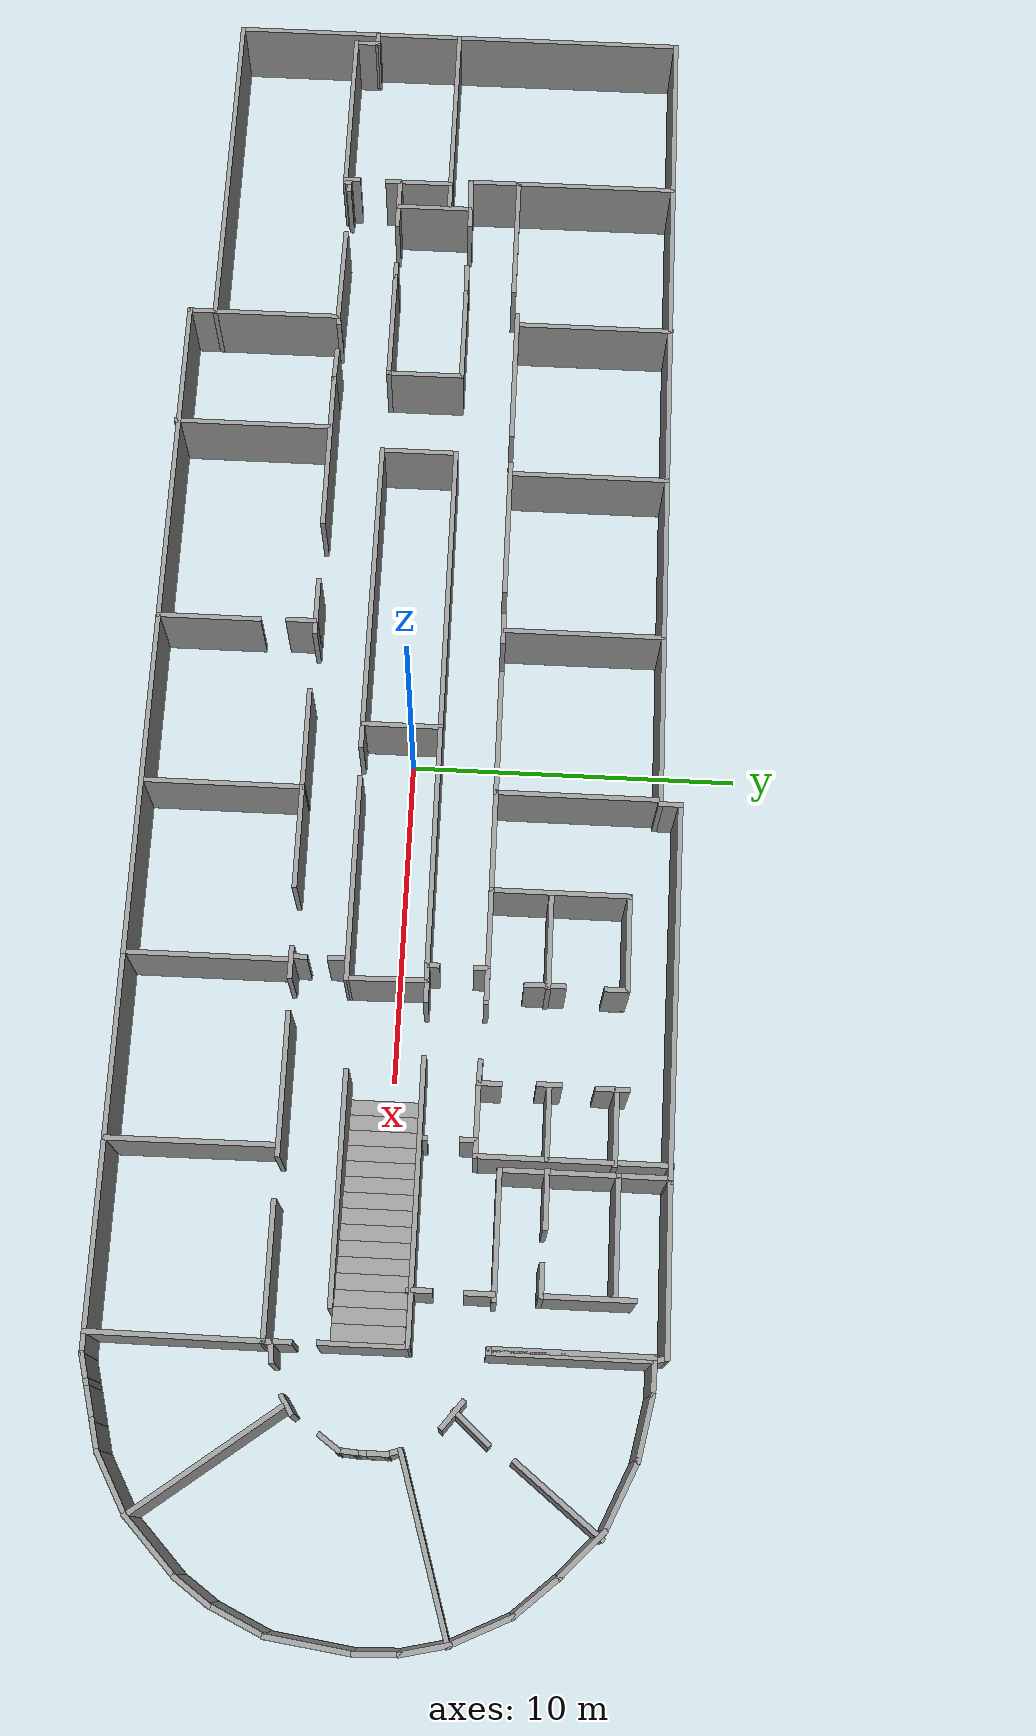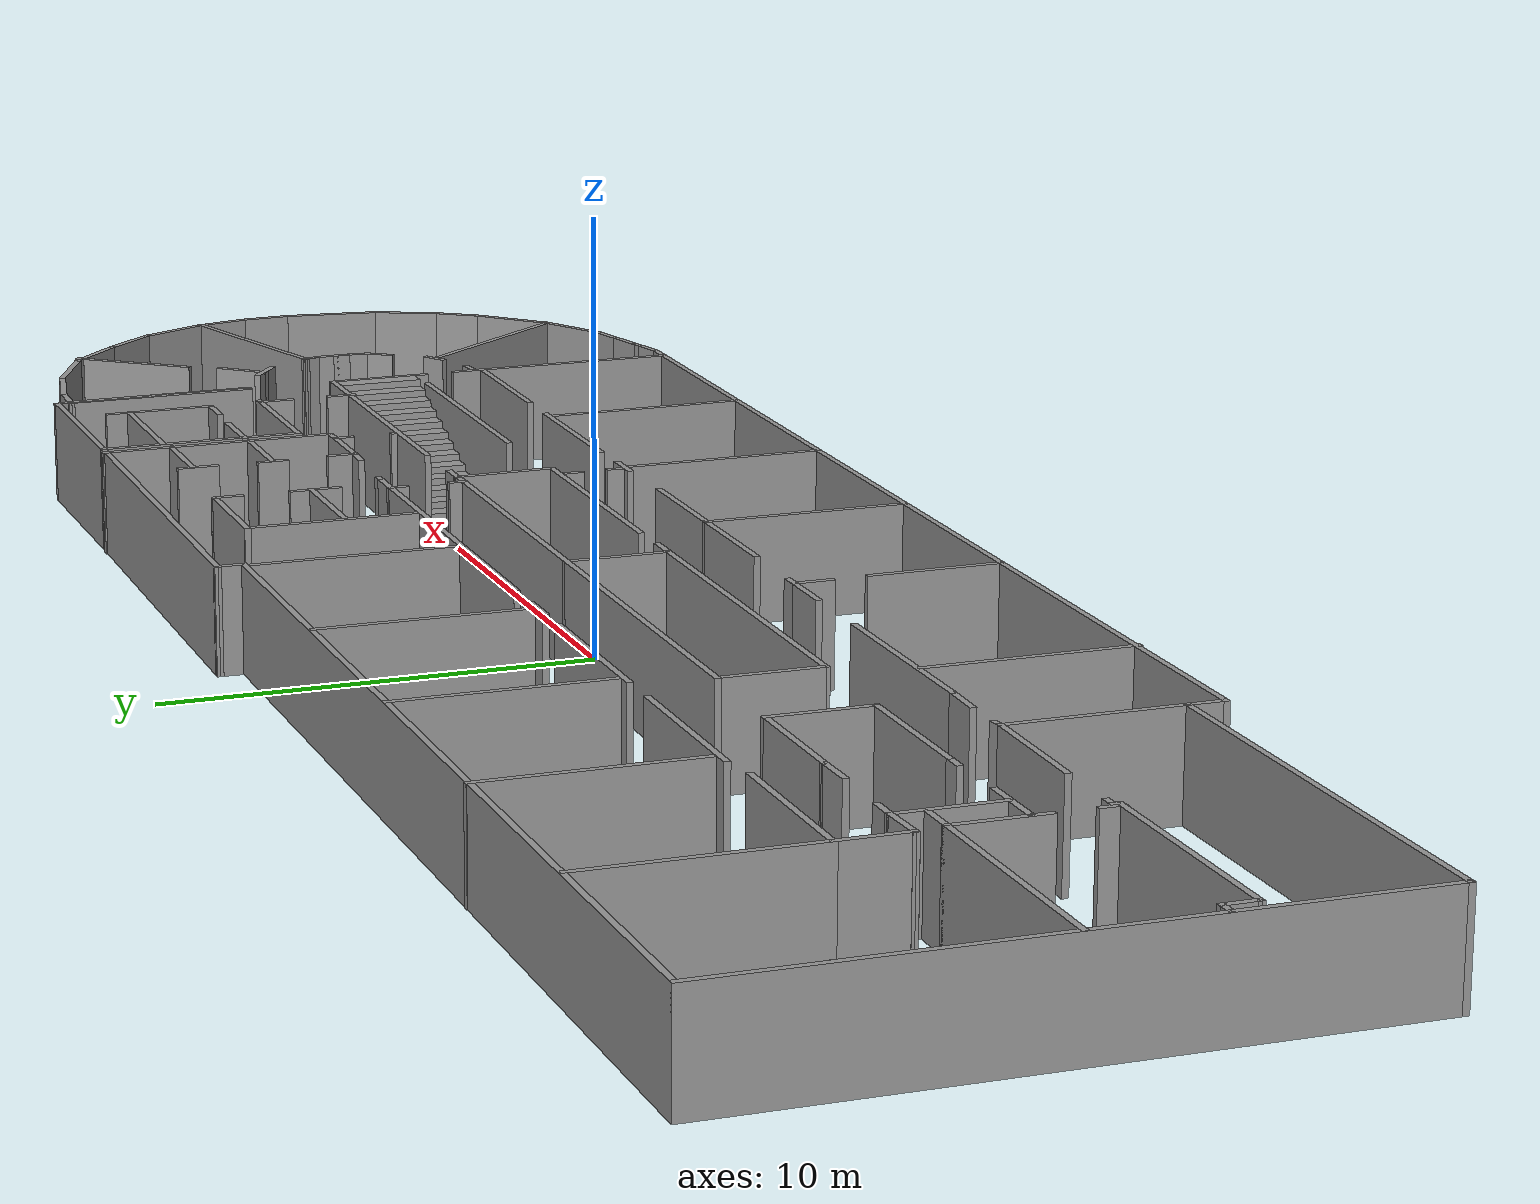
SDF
<?xml version='1.0'?>
<sdf version='1.7'>
  <model name='5OG_waende'>
    <pose>-0.0 0.0 0.0 0.0 -0 0</pose>
    <link name='Stairs_1'>
      <visual name='Stairs_1_Visual_0'>
        <pose>10.7982 -0.241611 0.083333 0 -0 1.5708</pose>
        <geometry>
          <box>
            <size>2.07123 0.478437 0.166667</size>
          </box>
        </geometry>
        <material>
          <script>
            <uri>file://media/materials/scripts/gazebo.material</uri>
            <name>Gazebo/Grey</name>
          </script>
          <ambient>1 1 1 1</ambient>
        </material>
        <meta>
          <layer>0</layer>
        </meta>
      </visual>
      <collision name='Stairs_1_Collision_0'>
        <geometry>
          <box>
            <size>2.07123 0.478437 0.166667</size>
          </box>
        </geometry>
        <pose>10.7982 -0.241611 0.083333 0 -0 1.5708</pose>
      </collision>
      <visual name='Stairs_1_Visual_1'>
        <pose>11.2766 -0.241611 0.25 0 -0 1.5708</pose>
        <geometry>
          <box>
            <size>2.07123 0.478437 0.166667</size>
          </box>
        </geometry>
        <material>
          <script>
            <uri>file://media/materials/scripts/gazebo.material</uri>
            <name>Gazebo/Grey</name>
          </script>
          <ambient>1 1 1 1</ambient>
        </material>
        <meta>
          <layer>0</layer>
        </meta>
      </visual>
      <collision name='Stairs_1_Collision_1'>
        <geometry>
          <box>
            <size>2.07123 0.478437 0.166667</size>
          </box>
        </geometry>
        <pose>11.2766 -0.241611 0.25 0 -0 1.5708</pose>
      </collision>
      <visual name='Stairs_1_Visual_2'>
        <pose>11.7551 -0.241611 0.416667 0 -0 1.5708</pose>
        <geometry>
          <box>
            <size>2.07123 0.478437 0.166667</size>
          </box>
        </geometry>
        <material>
          <script>
            <uri>file://media/materials/scripts/gazebo.material</uri>
            <name>Gazebo/Grey</name>
          </script>
          <ambient>1 1 1 1</ambient>
        </material>
        <meta>
          <layer>0</layer>
        </meta>
      </visual>
      <collision name='Stairs_1_Collision_2'>
        <geometry>
          <box>
            <size>2.07123 0.478437 0.166667</size>
          </box>
        </geometry>
        <pose>11.7551 -0.241611 0.416667 0 -0 1.5708</pose>
      </collision>
      <visual name='Stairs_1_Visual_3'>
        <pose>12.2335 -0.241611 0.583333 0 -0 1.5708</pose>
        <geometry>
          <box>
            <size>2.07123 0.478437 0.166667</size>
          </box>
        </geometry>
        <material>
          <script>
            <uri>file://media/materials/scripts/gazebo.material</uri>
            <name>Gazebo/Grey</name>
          </script>
          <ambient>1 1 1 1</ambient>
        </material>
        <meta>
          <layer>0</layer>
        </meta>
      </visual>
      <collision name='Stairs_1_Collision_3'>
        <geometry>
          <box>
            <size>2.07123 0.478437 0.166667</size>
          </box>
        </geometry>
        <pose>12.2335 -0.241611 0.583333 0 -0 1.5708</pose>
      </collision>
      <visual name='Stairs_1_Visual_4'>
        <pose>12.7119 -0.241611 0.75 0 -0 1.5708</pose>
        <geometry>
          <box>
            <size>2.07123 0.478437 0.166667</size>
          </box>
        </geometry>
        <material>
          <script>
            <uri>file://media/materials/scripts/gazebo.material</uri>
            <name>Gazebo/Grey</name>
          </script>
          <ambient>1 1 1 1</ambient>
        </material>
        <meta>
          <layer>0</layer>
        </meta>
      </visual>
      <collision name='Stairs_1_Collision_4'>
        <geometry>
          <box>
            <size>2.07123 0.478437 0.166667</size>
          </box>
        </geometry>
        <pose>12.7119 -0.241611 0.75 0 -0 1.5708</pose>
      </collision>
      <visual name='Stairs_1_Visual_5'>
        <pose>13.1904 -0.241611 0.916667 0 -0 1.5708</pose>
        <geometry>
          <box>
            <size>2.07123 0.478437 0.166667</size>
          </box>
        </geometry>
        <material>
          <script>
            <uri>file://media/materials/scripts/gazebo.material</uri>
            <name>Gazebo/Grey</name>
          </script>
          <ambient>1 1 1 1</ambient>
        </material>
        <meta>
          <layer>0</layer>
        </meta>
      </visual>
      <collision name='Stairs_1_Collision_5'>
        <geometry>
          <box>
            <size>2.07123 0.478437 0.166667</size>
          </box>
        </geometry>
        <pose>13.1904 -0.241611 0.916667 0 -0 1.5708</pose>
      </collision>
      <visual name='Stairs_1_Visual_6'>
        <pose>13.6688 -0.24161 1.08333 0 -0 1.5708</pose>
        <geometry>
          <box>
            <size>2.07123 0.478437 0.166667</size>
          </box>
        </geometry>
        <material>
          <script>
            <uri>file://media/materials/scripts/gazebo.material</uri>
            <name>Gazebo/Grey</name>
          </script>
          <ambient>1 1 1 1</ambient>
        </material>
        <meta>
          <layer>0</layer>
        </meta>
      </visual>
      <collision name='Stairs_1_Collision_6'>
        <geometry>
          <box>
            <size>2.07123 0.478437 0.166667</size>
          </box>
        </geometry>
        <pose>13.6688 -0.24161 1.08333 0 -0 1.5708</pose>
      </collision>
      <visual name='Stairs_1_Visual_7'>
        <pose>14.1472 -0.24161 1.25 0 -0 1.5708</pose>
        <geometry>
          <box>
            <size>2.07123 0.478437 0.166667</size>
          </box>
        </geometry>
        <material>
          <script>
            <uri>file://media/materials/scripts/gazebo.material</uri>
            <name>Gazebo/Grey</name>
          </script>
          <ambient>1 1 1 1</ambient>
        </material>
        <meta>
          <layer>0</layer>
        </meta>
      </visual>
      <collision name='Stairs_1_Collision_7'>
        <geometry>
          <box>
            <size>2.07123 0.478437 0.166667</size>
          </box>
        </geometry>
        <pose>14.1472 -0.24161 1.25 0 -0 1.5708</pose>
      </collision>
      <visual name='Stairs_1_Visual_8'>
        <pose>14.6257 -0.24161 1.41667 0 -0 1.5708</pose>
        <geometry>
          <box>
            <size>2.07123 0.478437 0.166667</size>
          </box>
        </geometry>
        <material>
          <script>
            <uri>file://media/materials/scripts/gazebo.material</uri>
            <name>Gazebo/Grey</name>
          </script>
          <ambient>1 1 1 1</ambient>
        </material>
        <meta>
          <layer>0</layer>
        </meta>
      </visual>
      <collision name='Stairs_1_Collision_8'>
        <geometry>
          <box>
            <size>2.07123 0.478437 0.166667</size>
          </box>
        </geometry>
        <pose>14.6257 -0.24161 1.41667 0 -0 1.5708</pose>
      </collision>
      <visual name='Stairs_1_Visual_9'>
        <pose>15.1041 -0.24161 1.58333 0 -0 1.5708</pose>
        <geometry>
          <box>
            <size>2.07123 0.478437 0.166667</size>
          </box>
        </geometry>
        <material>
          <script>
            <uri>file://media/materials/scripts/gazebo.material</uri>
            <name>Gazebo/Grey</name>
          </script>
          <ambient>1 1 1 1</ambient>
        </material>
        <meta>
          <layer>0</layer>
        </meta>
      </visual>
      <collision name='Stairs_1_Collision_9'>
        <geometry>
          <box>
            <size>2.07123 0.478437 0.166667</size>
          </box>
        </geometry>
        <pose>15.1041 -0.24161 1.58333 0 -0 1.5708</pose>
      </collision>
      <visual name='Stairs_1_Visual_10'>
        <pose>15.5826 -0.24161 1.75 0 -0 1.5708</pose>
        <geometry>
          <box>
            <size>2.07123 0.478437 0.166667</size>
          </box>
        </geometry>
        <material>
          <script>
            <uri>file://media/materials/scripts/gazebo.material</uri>
            <name>Gazebo/Grey</name>
          </script>
          <ambient>1 1 1 1</ambient>
        </material>
        <meta>
          <layer>0</layer>
        </meta>
      </visual>
      <collision name='Stairs_1_Collision_10'>
        <geometry>
          <box>
            <size>2.07123 0.478437 0.166667</size>
          </box>
        </geometry>
        <pose>15.5826 -0.24161 1.75 0 -0 1.5708</pose>
      </collision>
      <visual name='Stairs_1_Visual_11'>
        <pose>16.061 -0.24161 1.91667 0 -0 1.5708</pose>
        <geometry>
          <box>
            <size>2.07123 0.478437 0.166667</size>
          </box>
        </geometry>
        <material>
          <script>
            <uri>file://media/materials/scripts/gazebo.material</uri>
            <name>Gazebo/Grey</name>
          </script>
          <ambient>1 1 1 1</ambient>
        </material>
        <meta>
          <layer>0</layer>
        </meta>
      </visual>
      <collision name='Stairs_1_Collision_11'>
        <geometry>
          <box>
            <size>2.07123 0.478437 0.166667</size>
          </box>
        </geometry>
        <pose>16.061 -0.24161 1.91667 0 -0 1.5708</pose>
      </collision>
      <visual name='Stairs_1_Visual_12'>
        <pose>16.5394 -0.24161 2.08333 0 -0 1.5708</pose>
        <geometry>
          <box>
            <size>2.07123 0.478437 0.166667</size>
          </box>
        </geometry>
        <material>
          <script>
            <uri>file://media/materials/scripts/gazebo.material</uri>
            <name>Gazebo/Grey</name>
          </script>
          <ambient>1 1 1 1</ambient>
        </material>
        <meta>
          <layer>0</layer>
        </meta>
      </visual>
      <collision name='Stairs_1_Collision_12'>
        <geometry>
          <box>
            <size>2.07123 0.478437 0.166667</size>
          </box>
        </geometry>
        <pose>16.5394 -0.24161 2.08333 0 -0 1.5708</pose>
      </collision>
      <visual name='Stairs_1_Visual_13'>
        <pose>17.0179 -0.24161 2.25 0 -0 1.5708</pose>
        <geometry>
          <box>
            <size>2.07123 0.478437 0.166667</size>
          </box>
        </geometry>
        <material>
          <script>
            <uri>file://media/materials/scripts/gazebo.material</uri>
            <name>Gazebo/Grey</name>
          </script>
          <ambient>1 1 1 1</ambient>
        </material>
        <meta>
          <layer>0</layer>
        </meta>
      </visual>
      <collision name='Stairs_1_Collision_13'>
        <geometry>
          <box>
            <size>2.07123 0.478437 0.166667</size>
          </box>
        </geometry>
        <pose>17.0179 -0.24161 2.25 0 -0 1.5708</pose>
      </collision>
      <visual name='Stairs_1_Visual_14'>
        <pose>17.4963 -0.24161 2.41667 0 -0 1.5708</pose>
        <geometry>
          <box>
            <size>2.07123 0.478437 0.166667</size>
          </box>
        </geometry>
        <material>
          <script>
            <uri>file://media/materials/scripts/gazebo.material</uri>
            <name>Gazebo/Grey</name>
          </script>
          <ambient>1 1 1 1</ambient>
        </material>
        <meta>
          <layer>0</layer>
        </meta>
      </visual>
      <collision name='Stairs_1_Collision_14'>
        <geometry>
          <box>
            <size>2.07123 0.478437 0.166667</size>
          </box>
        </geometry>
        <pose>17.4963 -0.24161 2.41667 0 -0 1.5708</pose>
      </collision>
    </link>
    <link name='Wall_0'>
      <collision name='Wall_0_Collision'>
        <geometry>
          <box>
            <size>5 0.15 2.5</size>
          </box>
        </geometry>
        <pose>0 0 1.25 0 -0 0</pose>
      </collision>
      <visual name='Wall_0_Visual'>
        <pose>0 0 1.25 0 -0 0</pose>
        <geometry>
          <box>
            <size>5 0.15 2.5</size>
          </box>
        </geometry>
        <material>
          <script>
            <uri>file://media/materials/scripts/gazebo.material</uri>
            <name>Gazebo/Grey</name>
          </script>
          <ambient>1 1 1 1</ambient>
        </material>
        <meta>
          <layer>0</layer>
        </meta>
      </visual>
      <pose>-14.6424 -5.68764 0 0 -0 -1.5708</pose>
    </link>
    <link name='Wall_1'>
      <collision name='Wall_1_Collision'>
        <geometry>
          <box>
            <size>21.75 0.15 2.5</size>
          </box>
        </geometry>
        <pose>0 0 1.25 0 -0 0</pose>
      </collision>
      <visual name='Wall_1_Visual'>
        <pose>0 0 1.25 0 -0 0</pose>
        <geometry>
          <box>
            <size>21.75 0.15 2.5</size>
          </box>
        </geometry>
        <material>
          <script>
            <uri>file://media/materials/scripts/gazebo.material</uri>
            <name>Gazebo/Grey</name>
          </script>
          <ambient>1 1 1 1</ambient>
        </material>
        <meta>
          <layer>0</layer>
        </meta>
      </visual>
      <pose>-3.84243 -8.11264 0 0 -0 0</pose>
    </link>
    <link name='Wall_10'>
      <collision name='Wall_10_Collision'>
        <geometry>
          <box>
            <size>2.25 0.15 2.5</size>
          </box>
        </geometry>
        <pose>0 0 1.25 0 -0 0</pose>
      </collision>
      <visual name='Wall_10_Visual'>
        <pose>0 0 1.25 0 -0 0</pose>
        <geometry>
          <box>
            <size>2.25 0.15 2.5</size>
          </box>
        </geometry>
        <material>
          <script>
            <uri>file://media/materials/scripts/gazebo.material</uri>
            <name>Gazebo/Grey</name>
          </script>
          <ambient>1 1 1 1</ambient>
        </material>
        <meta>
          <layer>0</layer>
        </meta>
      </visual>
      <pose>23.3119 -5.75931 0 0 -0 0.785398</pose>
    </link>
    <link name='Wall_100'>
      <collision name='Wall_100_Collision'>
        <geometry>
          <box>
            <size>5 0.15 2.5</size>
          </box>
        </geometry>
        <pose>0 0 1.25 0 -0 0</pose>
      </collision>
      <visual name='Wall_100_Visual'>
        <pose>0 0 1.25 0 -0 0</pose>
        <geometry>
          <box>
            <size>5 0.15 2.5</size>
          </box>
        </geometry>
        <material>
          <script>
            <uri>file://media/materials/scripts/gazebo.material</uri>
            <name>Gazebo/Grey</name>
          </script>
          <ambient>1 1 1 1</ambient>
        </material>
        <meta>
          <layer>0</layer>
        </meta>
      </visual>
      <pose>-14.6211 5.15402 0 0 -0 -1.5708</pose>
    </link>
    <link name='Wall_102'>
      <collision name='Wall_102_Collision'>
        <geometry>
          <box>
            <size>5 0.15 2.5</size>
          </box>
        </geometry>
        <pose>0 0 1.25 0 -0 0</pose>
      </collision>
      <visual name='Wall_102_Visual'>
        <pose>0 0 1.25 0 -0 0</pose>
        <geometry>
          <box>
            <size>5 0.15 2.5</size>
          </box>
        </geometry>
        <material>
          <script>
            <uri>file://media/materials/scripts/gazebo.material</uri>
            <name>Gazebo/Grey</name>
          </script>
          <ambient>1 1 1 1</ambient>
        </material>
        <meta>
          <layer>0</layer>
        </meta>
      </visual>
      <pose>-9.21664 5.13653 0 0 -0 -1.5708</pose>
    </link>
    <link name='Wall_104'>
      <collision name='Wall_104_Collision'>
        <geometry>
          <box>
            <size>5 0.15 2.5</size>
          </box>
        </geometry>
        <pose>0 0 1.25 0 -0 0</pose>
      </collision>
      <visual name='Wall_104_Visual'>
        <pose>0 0 1.25 0 -0 0</pose>
        <geometry>
          <box>
            <size>5 0.15 2.5</size>
          </box>
        </geometry>
        <material>
          <script>
            <uri>file://media/materials/scripts/gazebo.material</uri>
            <name>Gazebo/Grey</name>
          </script>
          <ambient>1 1 1 1</ambient>
        </material>
        <meta>
          <layer>0</layer>
        </meta>
      </visual>
      <pose>-3.81222 5.10155 0 0 -0 -1.5708</pose>
    </link>
    <link name='Wall_106'>
      <collision name='Wall_106_Collision'>
        <geometry>
          <box>
            <size>3.25 0.15 2.5</size>
          </box>
        </geometry>
        <pose>0 0 1.25 0 -0 0</pose>
      </collision>
      <visual name='Wall_106_Visual'>
        <pose>0 0 1.25 0 -0 0</pose>
        <geometry>
          <box>
            <size>3.25 0.15 2.5</size>
          </box>
        </geometry>
        <material>
          <script>
            <uri>file://media/materials/scripts/gazebo.material</uri>
            <name>Gazebo/Grey</name>
          </script>
          <ambient>1 1 1 1</ambient>
        </material>
        <meta>
          <layer>0</layer>
        </meta>
      </visual>
      <pose>-14.1887 0.863741 0 0 -0 0</pose>
    </link>
    <link name='Wall_107'>
      <collision name='Wall_107_Collision'>
        <geometry>
          <box>
            <size>2.5 0.15 2.5</size>
          </box>
        </geometry>
        <pose>0 0 1.25 0 -0 0</pose>
      </collision>
      <visual name='Wall_107_Visual'>
        <pose>0 0 1.25 0 -0 0</pose>
        <geometry>
          <box>
            <size>2.5 0.15 2.5</size>
          </box>
        </geometry>
        <material>
          <script>
            <uri>file://media/materials/scripts/gazebo.material</uri>
            <name>Gazebo/Grey</name>
          </script>
          <ambient>1 1 1 1</ambient>
        </material>
        <meta>
          <layer>0</layer>
        </meta>
      </visual>
      <pose>-12.6387 -0.311259 0 0 -0 -1.5708</pose>
    </link>
    <link name='Wall_108'>
      <collision name='Wall_108_Collision'>
        <geometry>
          <box>
            <size>3.75 0.15 2.5</size>
          </box>
        </geometry>
        <pose>0 0 1.25 0 -0 0</pose>
      </collision>
      <visual name='Wall_108_Visual'>
        <pose>0 0 1.25 0 -0 0</pose>
        <geometry>
          <box>
            <size>3.75 0.15 2.5</size>
          </box>
        </geometry>
        <material>
          <script>
            <uri>file://media/materials/scripts/gazebo.material</uri>
            <name>Gazebo/Grey</name>
          </script>
          <ambient>1 1 1 1</ambient>
        </material>
        <meta>
          <layer>0</layer>
        </meta>
      </visual>
      <pose>-14.4387 -1.48626 0 0 -0 3.14159</pose>
    </link>
    <link name='Wall_11'>
      <collision name='Wall_11_Collision'>
        <geometry>
          <box>
            <size>1.33085 0.15 2.5</size>
          </box>
        </geometry>
        <pose>0 0 1.25 0 -0 0</pose>
      </collision>
      <visual name='Wall_11_Visual'>
        <pose>0 0 1.25 0 -0 0</pose>
        <geometry>
          <box>
            <size>1.33085 0.15 2.5</size>
          </box>
        </geometry>
        <material>
          <script>
            <uri>file://media/materials/scripts/gazebo.material</uri>
            <name>Gazebo/Grey</name>
          </script>
          <ambient>1 1 1 1</ambient>
        </material>
        <meta>
          <layer>0</layer>
        </meta>
      </visual>
      <pose>24.3861 -4.52841 0 0 -0 0.974205</pose>
    </link>
    <link name='Wall_110'>
      <collision name='Wall_110_Collision'>
        <geometry>
          <box>
            <size>3.28022 0.15 2.5</size>
          </box>
        </geometry>
        <pose>0 0 1.25 0 -0 0</pose>
      </collision>
      <visual name='Wall_110_Visual'>
        <pose>0 0 1.25 0 -0 0</pose>
        <geometry>
          <box>
            <size>3.28022 0.15 2.5</size>
          </box>
        </geometry>
        <material>
          <script>
            <uri>file://media/materials/scripts/gazebo.material</uri>
            <name>Gazebo/Grey</name>
          </script>
          <ambient>1 1 1 1</ambient>
        </material>
        <meta>
          <layer>0</layer>
        </meta>
      </visual>
      <pose>-16.2074 -3.23981 0 0 -0 -0.014586</pose>
    </link>
    <link name='Wall_112'>
      <collision name='Wall_112_Collision'>
        <geometry>
          <box>
            <size>1.17054 0.15 2.5</size>
          </box>
        </geometry>
        <pose>0 0 1.25 0 -0 0</pose>
      </collision>
      <visual name='Wall_112_Visual'>
        <pose>0 0 1.25 0 -0 0</pose>
        <geometry>
          <box>
            <size>1.17054 0.15 2.5</size>
          </box>
        </geometry>
        <material>
          <script>
            <uri>file://media/materials/scripts/gazebo.material</uri>
            <name>Gazebo/Grey</name>
          </script>
          <ambient>1 1 1 1</ambient>
        </material>
        <meta>
          <layer>0</layer>
        </meta>
      </visual>
      <pose>-12.8612 -3.2242 0 0 -0 -0.031116</pose>
    </link>
    <link name='Wall_114'>
      <collision name='Wall_114_Collision'>
        <geometry>
          <box>
            <size>0.382389 0.15 2.5</size>
          </box>
        </geometry>
        <pose>0 0 1.25 0 -0 0</pose>
      </collision>
      <visual name='Wall_114_Visual'>
        <pose>0 0 1.25 0 -0 0</pose>
        <geometry>
          <box>
            <size>0.382389 0.15 2.5</size>
          </box>
        </geometry>
        <material>
          <script>
            <uri>file://media/materials/scripts/gazebo.material</uri>
            <name>Gazebo/Grey</name>
          </script>
          <ambient>1 1 1 1</ambient>
        </material>
        <meta>
          <layer>0</layer>
        </meta>
      </visual>
      <pose>-14.5273 -3.24705 0 0 -0 -3.007</pose>
    </link>
    <link name='Wall_12'>
      <collision name='Wall_12_Collision'>
        <geometry>
          <box>
            <size>1.84074 0.15 2.5</size>
          </box>
        </geometry>
        <pose>0 0 1.25 0 -0 0</pose>
      </collision>
      <visual name='Wall_12_Visual'>
        <pose>0 0 1.25 0 -0 0</pose>
        <geometry>
          <box>
            <size>1.84074 0.15 2.5</size>
          </box>
        </geometry>
        <material>
          <script>
            <uri>file://media/materials/scripts/gazebo.material</uri>
            <name>Gazebo/Grey</name>
          </script>
          <ambient>1 1 1 1</ambient>
        </material>
        <meta>
          <layer>0</layer>
        </meta>
      </visual>
      <pose>25.0636 -3.26858 0 0 -0 1.14938</pose>
    </link>
    <link name='Wall_120'>
      <collision name='Wall_120_Collision'>
        <geometry>
          <box>
            <size>0.5 0.15 2.5</size>
          </box>
        </geometry>
        <pose>0 0 1.25 0 -0 0</pose>
      </collision>
      <visual name='Wall_120_Visual'>
        <pose>0 0 1.25 0 -0 0</pose>
        <geometry>
          <box>
            <size>0.5 0.15 2.5</size>
          </box>
        </geometry>
        <material>
          <script>
            <uri>file://media/materials/scripts/gazebo.material</uri>
            <name>Gazebo/Grey</name>
          </script>
          <ambient>1 1 1 1</ambient>
        </material>
        <meta>
          <layer>0</layer>
        </meta>
      </visual>
      <pose>-25.5475 -2.63736 0 0 -0 0</pose>
    </link>
    <link name='Wall_121'>
      <collision name='Wall_121_Collision'>
        <geometry>
          <box>
            <size>0.880662 0.15 2.5</size>
          </box>
        </geometry>
        <pose>0 0 1.25 0 -0 0</pose>
      </collision>
      <visual name='Wall_121_Visual'>
        <pose>0 0 1.25 0 -0 0</pose>
        <geometry>
          <box>
            <size>0.880662 0.15 2.5</size>
          </box>
        </geometry>
        <material>
          <script>
            <uri>file://media/materials/scripts/gazebo.material</uri>
            <name>Gazebo/Grey</name>
          </script>
          <ambient>1 1 1 1</ambient>
        </material>
        <meta>
          <layer>0</layer>
        </meta>
      </visual>
      <pose>-25.3726 -3.00237 0 0 -0 -1.57107</pose>
    </link>
    <link name='Wall_122'>
      <collision name='Wall_122_Collision'>
        <geometry>
          <box>
            <size>5.75 0.15 2.5</size>
          </box>
        </geometry>
        <pose>0 0 1.25 0 -0 0</pose>
      </collision>
      <visual name='Wall_122_Visual'>
        <pose>0 0 1.25 0 -0 0</pose>
        <geometry>
          <box>
            <size>5.75 0.15 2.5</size>
          </box>
        </geometry>
        <material>
          <script>
            <uri>file://media/materials/scripts/gazebo.material</uri>
            <name>Gazebo/Grey</name>
          </script>
          <ambient>1 1 1 1</ambient>
        </material>
        <meta>
          <layer>0</layer>
        </meta>
      </visual>
      <pose>-22.5727 -3.36738 0 0 -0 0</pose>
    </link>
    <link name='Wall_123'>
      <collision name='Wall_123_Collision'>
        <geometry>
          <box>
            <size>0.287406 0.15 2.5</size>
          </box>
        </geometry>
        <pose>0 0 1.25 0 -0 0</pose>
      </collision>
      <visual name='Wall_123_Visual'>
        <pose>0 0 1.25 0 -0 0</pose>
        <geometry>
          <box>
            <size>0.287406 0.15 2.5</size>
          </box>
        </geometry>
        <material>
          <script>
            <uri>file://media/materials/scripts/gazebo.material</uri>
            <name>Gazebo/Grey</name>
          </script>
          <ambient>1 1 1 1</ambient>
        </material>
        <meta>
          <layer>0</layer>
        </meta>
      </visual>
      <pose>-19.7667 -3.29894 0 0 -0 1.48314</pose>
    </link>
    <link name='Wall_124'>
      <collision name='Wall_124_Collision'>
        <geometry>
          <box>
            <size>0.408549 0.15 2.5</size>
          </box>
        </geometry>
        <pose>0 0 1.25 0 -0 0</pose>
      </collision>
      <visual name='Wall_124_Visual'>
        <pose>0 0 1.25 0 -0 0</pose>
        <geometry>
          <box>
            <size>0.408549 0.15 2.5</size>
          </box>
        </geometry>
        <material>
          <script>
            <uri>file://media/materials/scripts/gazebo.material</uri>
            <name>Gazebo/Grey</name>
          </script>
          <ambient>1 1 1 1</ambient>
        </material>
        <meta>
          <layer>0</layer>
        </meta>
      </visual>
      <pose>-19.6314 -3.2305 0 0 -0 0</pose>
    </link>
    <link name='Wall_127'>
      <collision name='Wall_127_Collision'>
        <geometry>
          <box>
            <size>0.591054 0.15 2.5</size>
          </box>
        </geometry>
        <pose>0 0 1.25 0 -0 0</pose>
      </collision>
      <visual name='Wall_127_Visual'>
        <pose>0 0 1.25 0 -0 0</pose>
        <geometry>
          <box>
            <size>0.591054 0.15 2.5</size>
          </box>
        </geometry>
        <material>
          <script>
            <uri>file://media/materials/scripts/gazebo.material</uri>
            <name>Gazebo/Grey</name>
          </script>
          <ambient>1 1 1 1</ambient>
        </material>
        <meta>
          <layer>0</layer>
        </meta>
      </visual>
      <pose>-19.8823 -3.16206 0 0 -0 -1.5708</pose>
    </link>
    <link name='Wall_129'>
      <collision name='Wall_129_Collision'>
        <geometry>
          <box>
            <size>6 0.15 2.5</size>
          </box>
        </geometry>
        <pose>0 0 1.25 0 -0 0</pose>
      </collision>
      <visual name='Wall_129_Visual'>
        <pose>0 0 1.25 0 -0 0</pose>
        <geometry>
          <box>
            <size>6 0.15 2.5</size>
          </box>
        </geometry>
        <material>
          <script>
            <uri>file://media/materials/scripts/gazebo.material</uri>
            <name>Gazebo/Grey</name>
          </script>
          <ambient>1 1 1 1</ambient>
        </material>
        <meta>
          <layer>0</layer>
        </meta>
      </visual>
      <pose>-22.7975 0.145843 0 0 -0 0</pose>
    </link>
    <link name='Wall_13'>
      <collision name='Wall_13_Collision'>
        <geometry>
          <box>
            <size>2.5652 0.15 2.5</size>
          </box>
        </geometry>
        <pose>0 0 1.25 0 -0 0</pose>
      </collision>
      <visual name='Wall_13_Visual'>
        <pose>0 0 1.25 0 -0 0</pose>
        <geometry>
          <box>
            <size>2.5652 0.15 2.5</size>
          </box>
        </geometry>
        <material>
          <script>
            <uri>file://media/materials/scripts/gazebo.material</uri>
            <name>Gazebo/Grey</name>
          </script>
          <ambient>1 1 1 1</ambient>
        </material>
        <meta>
          <layer>0</layer>
        </meta>
      </visual>
      <pose>25.569 -1.30016 0 0 -0 1.43824</pose>
    </link>
    <link name='Wall_130'>
      <collision name='Wall_130_Collision'>
        <geometry>
          <box>
            <size>2.25 0.15 2.5</size>
          </box>
        </geometry>
        <pose>0 0 1.25 0 -0 0</pose>
      </collision>
      <visual name='Wall_130_Visual'>
        <pose>0 0 1.25 0 -0 0</pose>
        <geometry>
          <box>
            <size>2.25 0.15 2.5</size>
          </box>
        </geometry>
        <material>
          <script>
            <uri>file://media/materials/scripts/gazebo.material</uri>
            <name>Gazebo/Grey</name>
          </script>
          <ambient>1 1 1 1</ambient>
        </material>
        <meta>
          <layer>0</layer>
        </meta>
      </visual>
      <pose>-19.8725 -0.904157 0 0 -0 -1.5708</pose>
    </link>
    <link name='Wall_132'>
      <collision name='Wall_132_Collision'>
        <geometry>
          <box>
            <size>1.75 0.15 2.5</size>
          </box>
        </geometry>
        <pose>0 0 1.25 0 -0 0</pose>
      </collision>
      <visual name='Wall_132_Visual'>
        <pose>0 0 1.25 0 -0 0</pose>
        <geometry>
          <box>
            <size>1.75 0.15 2.5</size>
          </box>
        </geometry>
        <material>
          <script>
            <uri>file://media/materials/scripts/gazebo.material</uri>
            <name>Gazebo/Grey</name>
          </script>
          <ambient>1 1 1 1</ambient>
        </material>
        <meta>
          <layer>0</layer>
        </meta>
      </visual>
      <pose>-19.0215 -1.54233 0 0 -0 0</pose>
    </link>
    <link name='Wall_134'>
      <collision name='Wall_134_Collision'>
        <geometry>
          <box>
            <size>2.5 0.15 2.5</size>
          </box>
        </geometry>
        <pose>0 0 1.25 0 -0 0</pose>
      </collision>
      <visual name='Wall_134_Visual'>
        <pose>0 0 1.25 0 -0 0</pose>
        <geometry>
          <box>
            <size>2.5 0.15 2.5</size>
          </box>
        </geometry>
        <material>
          <script>
            <uri>file://media/materials/scripts/gazebo.material</uri>
            <name>Gazebo/Grey</name>
          </script>
          <ambient>1 1 1 1</ambient>
        </material>
        <meta>
          <layer>0</layer>
        </meta>
      </visual>
      <pose>-18.9242 -0.314346 0 0 -0 -1.5708</pose>
    </link>
    <link name='Wall_136'>
      <collision name='Wall_136_Collision'>
        <geometry>
          <box>
            <size>1 0.15 2.5</size>
          </box>
        </geometry>
        <pose>0 0 1.25 0 -0 0</pose>
      </collision>
      <visual name='Wall_136_Visual'>
        <pose>0 0 1.25 0 -0 0</pose>
        <geometry>
          <box>
            <size>1 0.15 2.5</size>
          </box>
        </geometry>
        <material>
          <script>
            <uri>file://media/materials/scripts/gazebo.material</uri>
            <name>Gazebo/Grey</name>
          </script>
          <ambient>1 1 1 1</ambient>
        </material>
        <meta>
          <layer>0</layer>
        </meta>
      </visual>
      <pose>-19.4475 0.145843 0 0 -0 0</pose>
    </link>
    <link name='Wall_138'>
      <collision name='Wall_138_Collision'>
        <geometry>
          <box>
            <size>1.75 0.15 2.5</size>
          </box>
        </geometry>
        <pose>0 0 1.25 0 -0 0</pose>
      </collision>
      <visual name='Wall_138_Visual'>
        <pose>0 0 1.25 0 -0 0</pose>
        <geometry>
          <box>
            <size>1.75 0.15 2.5</size>
          </box>
        </geometry>
        <material>
          <script>
            <uri>file://media/materials/scripts/gazebo.material</uri>
            <name>Gazebo/Grey</name>
          </script>
          <ambient>1 1 1 1</ambient>
        </material>
        <meta>
          <layer>0</layer>
        </meta>
      </visual>
      <pose>-19.9838 1.61992 0 0 -0 -1.5708</pose>
    </link>
    <link name='Wall_139'>
      <collision name='Wall_139_Collision'>
        <geometry>
          <box>
            <size>1.21043 0.15 2.5</size>
          </box>
        </geometry>
        <pose>0 0 1.25 0 -0 0</pose>
      </collision>
      <visual name='Wall_139_Visual'>
        <pose>0 0 1.25 0 -0 0</pose>
        <geometry>
          <box>
            <size>1.21043 0.15 2.5</size>
          </box>
        </geometry>
        <material>
          <script>
            <uri>file://media/materials/scripts/gazebo.material</uri>
            <name>Gazebo/Grey</name>
          </script>
          <ambient>1 1 1 1</ambient>
        </material>
        <meta>
          <layer>0</layer>
        </meta>
      </visual>
      <pose>-19.454 0.840288 0 0 -0 0.038421</pose>
    </link>
    <link name='Wall_14'>
      <collision name='Wall_14_Collision'>
        <geometry>
          <box>
            <size>1.37477 0.15 2.5</size>
          </box>
        </geometry>
        <pose>0 0 1.25 0 -0 0</pose>
      </collision>
      <visual name='Wall_14_Visual'>
        <pose>0 0 1.25 0 -0 0</pose>
        <geometry>
          <box>
            <size>1.37477 0.15 2.5</size>
          </box>
        </geometry>
        <material>
          <script>
            <uri>file://media/materials/scripts/gazebo.material</uri>
            <name>Gazebo/Grey</name>
          </script>
          <ambient>1 1 1 1</ambient>
        </material>
        <meta>
          <layer>0</layer>
        </meta>
      </visual>
      <pose>25.702 0.508653 0 0 -0 1.61425</pose>
    </link>
    <link name='Wall_141'>
      <collision name='Wall_141_Collision'>
        <geometry>
          <box>
            <size>0.584617 0.15 2.5</size>
          </box>
        </geometry>
        <pose>0 0 1.25 0 -0 0</pose>
      </collision>
      <visual name='Wall_141_Visual'>
        <pose>0 0 1.25 0 -0 0</pose>
        <geometry>
          <box>
            <size>0.584617 0.15 2.5</size>
          </box>
        </geometry>
        <material>
          <script>
            <uri>file://media/materials/scripts/gazebo.material</uri>
            <name>Gazebo/Grey</name>
          </script>
          <ambient>1 1 1 1</ambient>
        </material>
        <meta>
          <layer>0</layer>
        </meta>
      </visual>
      <pose>-16.456 -1.48388 0 0 -0 -0.010965</pose>
    </link>
    <link name='Wall_143'>
      <collision name='Wall_143_Collision'>
        <geometry>
          <box>
            <size>1.08477 0.15 2.5</size>
          </box>
        </geometry>
        <pose>0 0 1.25 0 -0 0</pose>
      </collision>
      <visual name='Wall_143_Visual'>
        <pose>0 0 1.25 0 -0 0</pose>
        <geometry>
          <box>
            <size>1.08477 0.15 2.5</size>
          </box>
        </geometry>
        <material>
          <script>
            <uri>file://media/materials/scripts/gazebo.material</uri>
            <name>Gazebo/Grey</name>
          </script>
          <ambient>1 1 1 1</ambient>
        </material>
        <meta>
          <layer>0</layer>
        </meta>
      </visual>
      <pose>-16.206 0.854593 0 0 -0 0.019574</pose>
    </link>
    <link name='Wall_145'>
      <collision name='Wall_145_Collision'>
        <geometry>
          <box>
            <size>0.75 0.15 2.5</size>
          </box>
        </geometry>
        <pose>0 0 1.25 0 -0 0</pose>
      </collision>
      <visual name='Wall_145_Visual'>
        <pose>0 0 1.25 0 -0 0</pose>
        <geometry>
          <box>
            <size>0.75 0.15 2.5</size>
          </box>
        </geometry>
        <material>
          <script>
            <uri>file://media/materials/scripts/gazebo.material</uri>
            <name>Gazebo/Grey</name>
          </script>
          <ambient>1 1 1 1</ambient>
        </material>
        <meta>
          <layer>0</layer>
        </meta>
      </visual>
      <pose>-18.6242 0.860654 0 0 -0 0</pose>
    </link>
    <link name='Wall_147'>
      <collision name='Wall_147_Collision'>
        <geometry>
          <box>
            <size>1.5 0.15 2.5</size>
          </box>
        </geometry>
        <pose>0 0 1.25 0 -0 0</pose>
      </collision>
      <visual name='Wall_147_Visual'>
        <pose>0 0 1.25 0 -0 0</pose>
        <geometry>
          <box>
            <size>1.5 0.15 2.5</size>
          </box>
        </geometry>
        <material>
          <script>
            <uri>file://media/materials/scripts/gazebo.material</uri>
            <name>Gazebo/Grey</name>
          </script>
          <ambient>1 1 1 1</ambient>
        </material>
        <meta>
          <layer>0</layer>
        </meta>
      </visual>
      <pose>-4.52248 -3.2264 0 0 -0 0</pose>
    </link>
    <link name='Wall_148'>
      <collision name='Wall_148_Collision'>
        <geometry>
          <box>
            <size>1 0.15 2.5</size>
          </box>
        </geometry>
        <pose>0 0 1.25 0 -0 0</pose>
      </collision>
      <visual name='Wall_148_Visual'>
        <pose>0 0 1.25 0 -0 0</pose>
        <geometry>
          <box>
            <size>1 0.15 2.5</size>
          </box>
        </geometry>
        <material>
          <script>
            <uri>file://media/materials/scripts/gazebo.material</uri>
            <name>Gazebo/Grey</name>
          </script>
          <ambient>1 1 1 1</ambient>
        </material>
        <meta>
          <layer>0</layer>
        </meta>
      </visual>
      <pose>-3.84748 -3.6514 0 0 -0 -1.5708</pose>
    </link>
    <link name='Wall_15'>
      <collision name='Wall_15_Collision'>
        <geometry>
          <box>
            <size>1.48585 0.15 2.5</size>
          </box>
        </geometry>
        <pose>0 0 1.25 0 -0 0</pose>
      </collision>
      <visual name='Wall_15_Visual'>
        <pose>0 0 1.25 0 -0 0</pose>
        <geometry>
          <box>
            <size>1.48585 0.15 2.5</size>
          </box>
        </geometry>
        <material>
          <script>
            <uri>file://media/materials/scripts/gazebo.material</uri>
            <name>Gazebo/Grey</name>
          </script>
          <ambient>1 1 1 1</ambient>
        </material>
        <meta>
          <layer>0</layer>
        </meta>
      </visual>
      <pose>25.5291 1.77216 0 0 -0 1.79163</pose>
    </link>
    <link name='Wall_150'>
      <collision name='Wall_150_Collision'>
        <geometry>
          <box>
            <size>3.25 0.15 2.5</size>
          </box>
        </geometry>
        <pose>0 0 1.25 0 -0 0</pose>
      </collision>
      <visual name='Wall_150_Visual'>
        <pose>0 0 1.25 0 -0 0</pose>
        <geometry>
          <box>
            <size>3.25 0.15 2.5</size>
          </box>
        </geometry>
        <material>
          <script>
            <uri>file://media/materials/scripts/gazebo.material</uri>
            <name>Gazebo/Grey</name>
          </script>
          <ambient>1 1 1 1</ambient>
        </material>
        <meta>
          <layer>0</layer>
        </meta>
      </visual>
      <pose>-3.81348 -6.5432 0 0 -0 1.5708</pose>
    </link>
    <link name='Wall_152'>
      <collision name='Wall_152_Collision'>
        <geometry>
          <box>
            <size>0.5 0.15 2.5</size>
          </box>
        </geometry>
        <pose>0 0 1.25 0 -0 0</pose>
      </collision>
      <visual name='Wall_152_Visual'>
        <pose>0 0 1.25 0 -0 0</pose>
        <geometry>
          <box>
            <size>0.5 0.15 2.5</size>
          </box>
        </geometry>
        <material>
          <script>
            <uri>file://media/materials/scripts/gazebo.material</uri>
            <name>Gazebo/Grey</name>
          </script>
          <ambient>1 1 1 1</ambient>
        </material>
        <meta>
          <layer>0</layer>
        </meta>
      </visual>
      <pose>-3.67247 -3.2264 0 0 -0 0</pose>
    </link>
    <link name='Wall_154'>
      <collision name='Wall_154_Collision'>
        <geometry>
          <box>
            <size>5 0.15 2.5</size>
          </box>
        </geometry>
        <pose>0 0 1.25 0 -0 0</pose>
      </collision>
      <visual name='Wall_154_Visual'>
        <pose>0 0 1.25 0 -0 0</pose>
        <geometry>
          <box>
            <size>5 0.15 2.5</size>
          </box>
        </geometry>
        <material>
          <script>
            <uri>file://media/materials/scripts/gazebo.material</uri>
            <name>Gazebo/Grey</name>
          </script>
          <ambient>1 1 1 1</ambient>
        </material>
        <meta>
          <layer>0</layer>
        </meta>
      </visual>
      <pose>1.60084 -5.6682 0 0 -0 1.5708</pose>
    </link>
    <link name='Wall_155'>
      <collision name='Wall_155_Collision'>
        <geometry>
          <box>
            <size>3.25 0.15 2.5</size>
          </box>
        </geometry>
        <pose>0 0 1.25 0 -0 0</pose>
      </collision>
      <visual name='Wall_155_Visual'>
        <pose>0 0 1.25 0 -0 0</pose>
        <geometry>
          <box>
            <size>3.25 0.15 2.5</size>
          </box>
        </geometry>
        <material>
          <script>
            <uri>file://media/materials/scripts/gazebo.material</uri>
            <name>Gazebo/Grey</name>
          </script>
          <ambient>1 1 1 1</ambient>
        </material>
        <meta>
          <layer>0</layer>
        </meta>
      </visual>
      <pose>0.050837 -3.2432 0 0 -0 3.14159</pose>
    </link>
    <link name='Wall_157'>
      <collision name='Wall_157_Collision'>
        <geometry>
          <box>
            <size>3.25 0.15 2.5</size>
          </box>
        </geometry>
        <pose>0 0 1.25 0 -0 0</pose>
      </collision>
      <visual name='Wall_157_Visual'>
        <pose>0 0 1.25 0 -0 0</pose>
        <geometry>
          <box>
            <size>3.25 0.15 2.5</size>
          </box>
        </geometry>
        <material>
          <script>
            <uri>file://media/materials/scripts/gazebo.material</uri>
            <name>Gazebo/Grey</name>
          </script>
          <ambient>1 1 1 1</ambient>
        </material>
        <meta>
          <layer>0</layer>
        </meta>
      </visual>
      <pose>3.15084 -3.2432 0 0 -0 0</pose>
    </link>
    <link name='Wall_159'>
      <collision name='Wall_159_Collision'>
        <geometry>
          <box>
            <size>5 0.15 2.5</size>
          </box>
        </geometry>
        <pose>0 0 1.25 0 -0 0</pose>
      </collision>
      <visual name='Wall_159_Visual'>
        <pose>0 0 1.25 0 -0 0</pose>
        <geometry>
          <box>
            <size>5 0.15 2.5</size>
          </box>
        </geometry>
        <material>
          <script>
            <uri>file://media/materials/scripts/gazebo.material</uri>
            <name>Gazebo/Grey</name>
          </script>
          <ambient>1 1 1 1</ambient>
        </material>
        <meta>
          <layer>0</layer>
        </meta>
      </visual>
      <pose>6.95757 -5.68764 0 0 -0 1.5708</pose>
    </link>
    <link name='Wall_161'>
      <collision name='Wall_161_Collision'>
        <geometry>
          <box>
            <size>1 0.15 2.5</size>
          </box>
        </geometry>
        <pose>0 0 1.25 0 -0 0</pose>
      </collision>
      <visual name='Wall_161_Visual'>
        <pose>0 0 1.25 0 -0 0</pose>
        <geometry>
          <box>
            <size>1 0.15 2.5</size>
          </box>
        </geometry>
        <material>
          <script>
            <uri>file://media/materials/scripts/gazebo.material</uri>
            <name>Gazebo/Grey</name>
          </script>
          <ambient>1 1 1 1</ambient>
        </material>
        <meta>
          <layer>0</layer>
        </meta>
      </visual>
      <pose>7.02951 -3.18077 0 0 -0 0</pose>
    </link>
    <link name='Wall_165'>
      <collision name='Wall_165_Collision'>
        <geometry>
          <box>
            <size>0.560918 0.15 2.5</size>
          </box>
        </geometry>
        <pose>0 0 1.25 0 -0 0</pose>
      </collision>
      <visual name='Wall_165_Visual'>
        <pose>0 0 1.25 0 -0 0</pose>
        <geometry>
          <box>
            <size>0.560918 0.15 2.5</size>
          </box>
        </geometry>
        <material>
          <script>
            <uri>file://media/materials/scripts/gazebo.material</uri>
            <name>Gazebo/Grey</name>
          </script>
          <ambient>1 1 1 1</ambient>
        </material>
        <meta>
          <layer>0</layer>
        </meta>
      </visual>
      <pose>6.85546 -2.97545 0 0 -0 -1.60782</pose>
    </link>
    <link name='Wall_167'>
      <collision name='Wall_167_Collision'>
        <geometry>
          <box>
            <size>0.5 0.15 2.5</size>
          </box>
        </geometry>
        <pose>0 0 1.25 0 -0 0</pose>
      </collision>
      <visual name='Wall_167_Visual'>
        <pose>0 0 1.25 0 -0 0</pose>
        <geometry>
          <box>
            <size>0.5 0.15 2.5</size>
          </box>
        </geometry>
        <material>
          <script>
            <uri>file://media/materials/scripts/gazebo.material</uri>
            <name>Gazebo/Grey</name>
          </script>
          <ambient>1 1 1 1</ambient>
        </material>
        <meta>
          <layer>0</layer>
        </meta>
      </visual>
      <pose>6.84786 -1.86511 0 0 -0 1.5708</pose>
    </link>
    <link name='Wall_169'>
      <collision name='Wall_169_Collision'>
        <geometry>
          <box>
            <size>4.25 0.15 2.5</size>
          </box>
        </geometry>
        <pose>0 0 1.25 0 -0 0</pose>
      </collision>
      <visual name='Wall_169_Visual'>
        <pose>0 0 1.25 0 -0 0</pose>
        <geometry>
          <box>
            <size>4.25 0.15 2.5</size>
          </box>
        </geometry>
        <material>
          <script>
            <uri>file://media/materials/scripts/gazebo.material</uri>
            <name>Gazebo/Grey</name>
          </script>
          <ambient>1 1 1 1</ambient>
        </material>
        <meta>
          <layer>0</layer>
        </meta>
      </visual>
      <pose>10.6164 -3.13514 0 0 -0 0</pose>
    </link>
    <link name='Wall_17'>
      <collision name='Wall_17_Collision'>
        <geometry>
          <box>
            <size>1.97402 0.15 2.5</size>
          </box>
        </geometry>
        <pose>0 0 1.25 0 -0 0</pose>
      </collision>
      <visual name='Wall_17_Visual'>
        <pose>0 0 1.25 0 -0 0</pose>
        <geometry>
          <box>
            <size>1.97402 0.15 2.5</size>
          </box>
        </geometry>
        <material>
          <script>
            <uri>file://media/materials/scripts/gazebo.material</uri>
            <name>Gazebo/Grey</name>
          </script>
          <ambient>1 1 1 1</ambient>
        </material>
        <meta>
          <layer>0</layer>
        </meta>
      </visual>
      <pose>24.9959 3.24973 0 0 -0 2.00893</pose>
    </link>
    <link name='Wall_172'>
      <collision name='Wall_172_Collision'>
        <geometry>
          <box>
            <size>5.06245 0.15 2.5</size>
          </box>
        </geometry>
        <pose>0 0 1.25 0 -0 0</pose>
      </collision>
      <visual name='Wall_172_Visual'>
        <pose>0 0 1.25 0 -0 0</pose>
        <geometry>
          <box>
            <size>5.06245 0.15 2.5</size>
          </box>
        </geometry>
        <material>
          <script>
            <uri>file://media/materials/scripts/gazebo.material</uri>
            <name>Gazebo/Grey</name>
          </script>
          <ambient>1 1 1 1</ambient>
        </material>
        <meta>
          <layer>0</layer>
        </meta>
      </visual>
      <pose>12.4143 -5.60656 0 0 -0 1.57699</pose>
    </link>
    <link name='Wall_174'>
      <collision name='Wall_174_Collision'>
        <geometry>
          <box>
            <size>4 0.15 2.5</size>
          </box>
        </geometry>
        <pose>0 0 1.25 0 -0 0</pose>
      </collision>
      <visual name='Wall_174_Visual'>
        <pose>0 0 1.25 0 -0 0</pose>
        <geometry>
          <box>
            <size>4 0.15 2.5</size>
          </box>
        </geometry>
        <material>
          <script>
            <uri>file://media/materials/scripts/gazebo.material</uri>
            <name>Gazebo/Grey</name>
          </script>
          <ambient>1 1 1 1</ambient>
        </material>
        <meta>
          <layer>0</layer>
        </meta>
      </visual>
      <pose>15.9058 -3.13514 0 0 -0 0</pose>
    </link>
    <link name='Wall_175'>
      <collision name='Wall_175_Collision'>
        <geometry>
          <box>
            <size>5.12755 0.15 2.5</size>
          </box>
        </geometry>
        <pose>0 0 1.25 0 -0 0</pose>
      </collision>
      <visual name='Wall_175_Visual'>
        <pose>0 0 1.25 0 -0 0</pose>
        <geometry>
          <box>
            <size>5.12755 0.15 2.5</size>
          </box>
        </geometry>
        <material>
          <script>
            <uri>file://media/materials/scripts/gazebo.material</uri>
            <name>Gazebo/Grey</name>
          </script>
          <ambient>1 1 1 1</ambient>
        </material>
        <meta>
          <layer>0</layer>
        </meta>
      </visual>
      <pose>17.8192 -5.62389 0 0 -0 -1.57546</pose>
    </link>
    <link name='Wall_177'>
      <collision name='Wall_177_Collision'>
        <geometry>
          <box>
            <size>0.885695 0.15 2.5</size>
          </box>
        </geometry>
        <pose>0 0 1.25 0 -0 0</pose>
      </collision>
      <visual name='Wall_177_Visual'>
        <pose>0 0 1.25 0 -0 0</pose>
        <geometry>
          <box>
            <size>0.885695 0.15 2.5</size>
          </box>
        </geometry>
        <material>
          <script>
            <uri>file://media/materials/scripts/gazebo.material</uri>
            <name>Gazebo/Grey</name>
          </script>
          <ambient>1 1 1 1</ambient>
        </material>
        <meta>
          <layer>0</layer>
        </meta>
      </visual>
      <pose>17.8268 -2.76732 0 0 -0 -1.56005</pose>
    </link>
    <link name='Wall_18'>
      <collision name='Wall_18_Collision'>
        <geometry>
          <box>
            <size>1.75604 0.15 2.5</size>
          </box>
        </geometry>
        <pose>0 0 1.25 0 -0 0</pose>
      </collision>
      <visual name='Wall_18_Visual'>
        <pose>0 0 1.25 0 -0 0</pose>
        <geometry>
          <box>
            <size>1.75604 0.15 2.5</size>
          </box>
        </geometry>
        <material>
          <script>
            <uri>file://media/materials/scripts/gazebo.material</uri>
            <name>Gazebo/Grey</name>
          </script>
          <ambient>1 1 1 1</ambient>
        </material>
        <meta>
          <layer>0</layer>
        </meta>
      </visual>
      <pose>24.083 4.68243 0 0 -0 2.28489</pose>
    </link>
    <link name='Wall_181'>
      <collision name='Wall_181_Collision'>
        <geometry>
          <box>
            <size>0.643773 0.15 2.5</size>
          </box>
        </geometry>
        <pose>0 0 1.25 0 -0 0</pose>
      </collision>
      <visual name='Wall_181_Visual'>
        <pose>0 0 1.25 0 -0 0</pose>
        <geometry>
          <box>
            <size>0.643773 0.15 2.5</size>
          </box>
        </geometry>
        <material>
          <script>
            <uri>file://media/materials/scripts/gazebo.material</uri>
            <name>Gazebo/Grey</name>
          </script>
          <ambient>1 1 1 1</ambient>
        </material>
        <meta>
          <layer>0</layer>
        </meta>
      </visual>
      <pose>18.094 -2.89543 0 0 -0 -3.00727</pose>
    </link>
    <link name='Wall_184'>
      <collision name='Wall_184_Collision'>
        <geometry>
          <box>
            <size>0.656191 0.15 2.5</size>
          </box>
        </geometry>
        <pose>0 0 1.25 0 -0 0</pose>
      </collision>
      <visual name='Wall_184_Visual'>
        <pose>0 0 1.25 0 -0 0</pose>
        <geometry>
          <box>
            <size>0.656191 0.15 2.5</size>
          </box>
        </geometry>
        <material>
          <script>
            <uri>file://media/materials/scripts/gazebo.material</uri>
            <name>Gazebo/Grey</name>
          </script>
          <ambient>1 1 1 1</ambient>
        </material>
        <meta>
          <layer>0</layer>
        </meta>
      </visual>
      <pose>19.4892 -2.36643 0 0 -0 0.580756</pose>
    </link>
    <link name='Wall_186'>
      <collision name='Wall_186_Collision'>
        <geometry>
          <box>
            <size>6.75 0.15 2.5</size>
          </box>
        </geometry>
        <pose>0 0 1.25 0 -0 0</pose>
      </collision>
      <visual name='Wall_186_Visual'>
        <pose>0 0 1.25 0 -0 0</pose>
        <geometry>
          <box>
            <size>6.75 0.15 2.5</size>
          </box>
        </geometry>
        <material>
          <script>
            <uri>file://media/materials/scripts/gazebo.material</uri>
            <name>Gazebo/Grey</name>
          </script>
          <ambient>1 1 1 1</ambient>
        </material>
        <meta>
          <layer>0</layer>
        </meta>
      </visual>
      <pose>13.4788 -1.34149 0 0 -0 0</pose>
    </link>
    <link name='Wall_188'>
      <collision name='Wall_188_Collision'>
        <geometry>
          <box>
            <size>2.60999 0.15 2.5</size>
          </box>
        </geometry>
        <pose>0 0 1.25 0 -0 0</pose>
      </collision>
      <visual name='Wall_188_Visual'>
        <pose>0 0 1.25 0 -0 0</pose>
        <geometry>
          <box>
            <size>2.60999 0.15 2.5</size>
          </box>
        </geometry>
        <material>
          <script>
            <uri>file://media/materials/scripts/gazebo.material</uri>
            <name>Gazebo/Grey</name>
          </script>
          <ambient>1 1 1 1</ambient>
        </material>
        <meta>
          <layer>0</layer>
        </meta>
      </visual>
      <pose>17.7898 -0.349615 0 0 -0 1.57617</pose>
    </link>
    <link name='Wall_189'>
      <collision name='Wall_189_Collision'>
        <geometry>
          <box>
            <size>8.25 0.15 2.5</size>
          </box>
        </geometry>
        <pose>0 0 1.25 0 -0 0</pose>
      </collision>
      <visual name='Wall_189_Visual'>
        <pose>0 0 1.25 0 -0 0</pose>
        <geometry>
          <box>
            <size>8.25 0.15 2.5</size>
          </box>
        </geometry>
        <material>
          <script>
            <uri>file://media/materials/scripts/gazebo.material</uri>
            <name>Gazebo/Grey</name>
          </script>
          <ambient>1 1 1 1</ambient>
        </material>
        <meta>
          <layer>0</layer>
        </meta>
      </visual>
      <pose>13.7332 0.88031 0 0 -0 3.14159</pose>
    </link>
    <link name='Wall_19'>
      <collision name='Wall_19_Collision'>
        <geometry>
          <box>
            <size>1.83802 0.15 2.5</size>
          </box>
        </geometry>
        <pose>0 0 1.25 0 -0 0</pose>
      </collision>
      <visual name='Wall_19_Visual'>
        <pose>0 0 1.25 0 -0 0</pose>
        <geometry>
          <box>
            <size>1.83802 0.15 2.5</size>
          </box>
        </geometry>
        <material>
          <script>
            <uri>file://media/materials/scripts/gazebo.material</uri>
            <name>Gazebo/Grey</name>
          </script>
          <ambient>1 1 1 1</ambient>
        </material>
        <meta>
          <layer>0</layer>
        </meta>
      </visual>
      <pose>22.9503 5.87587 0 0 -0 2.37314</pose>
    </link>
    <link name='Wall_191'>
      <collision name='Wall_191_Collision'>
        <geometry>
          <box>
            <size>0.75 0.15 2.5</size>
          </box>
        </geometry>
        <pose>0 0 1.25 0 -0 0</pose>
      </collision>
      <visual name='Wall_191_Visual'>
        <pose>0 0 1.25 0 -0 0</pose>
        <geometry>
          <box>
            <size>0.75 0.15 2.5</size>
          </box>
        </geometry>
        <material>
          <script>
            <uri>file://media/materials/scripts/gazebo.material</uri>
            <name>Gazebo/Grey</name>
          </script>
          <ambient>1 1 1 1</ambient>
        </material>
        <meta>
          <layer>0</layer>
        </meta>
      </visual>
      <pose>7.68034 0.842025 0 0 -0 0</pose>
    </link>
    <link name='Wall_194'>
      <collision name='Wall_194_Collision'>
        <geometry>
          <box>
            <size>4.25 0.15 2.5</size>
          </box>
        </geometry>
        <pose>0 0 1.25 0 -0 0</pose>
      </collision>
      <visual name='Wall_194_Visual'>
        <pose>0 0 1.25 0 -0 0</pose>
        <geometry>
          <box>
            <size>4.25 0.15 2.5</size>
          </box>
        </geometry>
        <material>
          <script>
            <uri>file://media/materials/scripts/gazebo.material</uri>
            <name>Gazebo/Grey</name>
          </script>
          <ambient>1 1 1 1</ambient>
        </material>
        <meta>
          <layer>0</layer>
        </meta>
      </visual>
      <pose>4.54735 4.65508 0 0 -0 -1.5708</pose>
    </link>
    <link name='Wall_196'>
      <collision name='Wall_196_Collision'>
        <geometry>
          <box>
            <size>3 0.15 2.5</size>
          </box>
        </geometry>
        <pose>0 0 1.25 0 -0 0</pose>
      </collision>
      <visual name='Wall_196_Visual'>
        <pose>0 0 1.25 0 -0 0</pose>
        <geometry>
          <box>
            <size>3 0.15 2.5</size>
          </box>
        </geometry>
        <material>
          <script>
            <uri>file://media/materials/scripts/gazebo.material</uri>
            <name>Gazebo/Grey</name>
          </script>
          <ambient>1 1 1 1</ambient>
        </material>
        <meta>
          <layer>0</layer>
        </meta>
      </visual>
      <pose>5.97235 6.70508 0 0 -0 0</pose>
    </link>
    <link name='Wall_197'>
      <collision name='Wall_197_Collision'>
        <geometry>
          <box>
            <size>0.75 0.15 2.5</size>
          </box>
        </geometry>
        <pose>0 0 1.25 0 -0 0</pose>
      </collision>
      <visual name='Wall_197_Visual'>
        <pose>0 0 1.25 0 -0 0</pose>
        <geometry>
          <box>
            <size>0.75 0.15 2.5</size>
          </box>
        </geometry>
        <material>
          <script>
            <uri>file://media/materials/scripts/gazebo.material</uri>
            <name>Gazebo/Grey</name>
          </script>
          <ambient>1 1 1 1</ambient>
        </material>
        <meta>
          <layer>0</layer>
        </meta>
      </visual>
      <pose>7.39735 6.40508 0 0 -0 -1.5708</pose>
    </link>
    <link name='Wall_199'>
      <collision name='Wall_199_Collision'>
        <geometry>
          <box>
            <size>1.25 0.15 2.5</size>
          </box>
        </geometry>
        <pose>0 0 1.25 0 -0 0</pose>
      </collision>
      <visual name='Wall_199_Visual'>
        <pose>0 0 1.25 0 -0 0</pose>
        <geometry>
          <box>
            <size>1.25 0.15 2.5</size>
          </box>
        </geometry>
        <material>
          <script>
            <uri>file://media/materials/scripts/gazebo.material</uri>
            <name>Gazebo/Grey</name>
          </script>
          <ambient>1 1 1 1</ambient>
        </material>
        <meta>
          <layer>0</layer>
        </meta>
      </visual>
      <pose>7.36928 4.30463 0 0 -0 -1.5708</pose>
    </link>
    <link name='Wall_20'>
      <collision name='Wall_20_Collision'>
        <geometry>
          <box>
            <size>2.19571 0.15 2.5</size>
          </box>
        </geometry>
        <pose>0 0 1.25 0 -0 0</pose>
      </collision>
      <visual name='Wall_20_Visual'>
        <pose>0 0 1.25 0 -0 0</pose>
        <geometry>
          <box>
            <size>2.19571 0.15 2.5</size>
          </box>
        </geometry>
        <material>
          <script>
            <uri>file://media/materials/scripts/gazebo.material</uri>
            <name>Gazebo/Grey</name>
          </script>
          <ambient>1 1 1 1</ambient>
        </material>
        <meta>
          <layer>0</layer>
        </meta>
      </visual>
      <pose>21.4129 6.88726 0 0 -0 2.71333</pose>
    </link>
    <link name='Wall_201'>
      <collision name='Wall_201_Collision'>
        <geometry>
          <box>
            <size>3 0.15 2.5</size>
          </box>
        </geometry>
        <pose>0 0 1.25 0 -0 0</pose>
      </collision>
      <visual name='Wall_201_Visual'>
        <pose>0 0 1.25 0 -0 0</pose>
        <geometry>
          <box>
            <size>3 0.15 2.5</size>
          </box>
        </geometry>
        <material>
          <script>
            <uri>file://media/materials/scripts/gazebo.material</uri>
            <name>Gazebo/Grey</name>
          </script>
          <ambient>1 1 1 1</ambient>
        </material>
        <meta>
          <layer>0</layer>
        </meta>
      </visual>
      <pose>5.99548 4.39202 0 0 -0 0</pose>
    </link>
    <link name='Wall_203'>
      <collision name='Wall_203_Collision'>
        <geometry>
          <box>
            <size>5.75 0.15 2.5</size>
          </box>
        </geometry>
        <pose>0 0 1.25 0 -0 0</pose>
      </collision>
      <visual name='Wall_203_Visual'>
        <pose>0 0 1.25 0 -0 0</pose>
        <geometry>
          <box>
            <size>5.75 0.15 2.5</size>
          </box>
        </geometry>
        <material>
          <script>
            <uri>file://media/materials/scripts/gazebo.material</uri>
            <name>Gazebo/Grey</name>
          </script>
          <ambient>1 1 1 1</ambient>
        </material>
        <meta>
          <layer>0</layer>
        </meta>
      </visual>
      <pose>12.4349 5.29292 0 0 -0 -1.5708</pose>
    </link>
    <link name='Wall_204'>
      <collision name='Wall_204_Collision'>
        <geometry>
          <box>
            <size>2.25 0.15 2.5</size>
          </box>
        </geometry>
        <pose>0 0 1.25 0 -0 0</pose>
      </collision>
      <visual name='Wall_204_Visual'>
        <pose>0 0 1.25 0 -0 0</pose>
        <geometry>
          <box>
            <size>2.25 0.15 2.5</size>
          </box>
        </geometry>
        <material>
          <script>
            <uri>file://media/materials/scripts/gazebo.material</uri>
            <name>Gazebo/Grey</name>
          </script>
          <ambient>1 1 1 1</ambient>
        </material>
        <meta>
          <layer>0</layer>
        </meta>
      </visual>
      <pose>11.3849 2.49292 0 0 -0 3.14159</pose>
    </link>
    <link name='Wall_205'>
      <collision name='Wall_205_Collision'>
        <geometry>
          <box>
            <size>0.75 0.15 2.5</size>
          </box>
        </geometry>
        <pose>0 0 1.25 0 -0 0</pose>
      </collision>
      <visual name='Wall_205_Visual'>
        <pose>0 0 1.25 0 -0 0</pose>
        <geometry>
          <box>
            <size>0.75 0.15 2.5</size>
          </box>
        </geometry>
        <material>
          <script>
            <uri>file://media/materials/scripts/gazebo.material</uri>
            <name>Gazebo/Grey</name>
          </script>
          <ambient>1 1 1 1</ambient>
        </material>
        <meta>
          <layer>0</layer>
        </meta>
      </visual>
      <pose>10.3349 2.79292 0 0 -0 1.5708</pose>
    </link>
    <link name='Wall_207'>
      <collision name='Wall_207_Collision'>
        <geometry>
          <box>
            <size>0.75 0.15 2.5</size>
          </box>
        </geometry>
        <pose>0 0 1.25 0 -0 0</pose>
      </collision>
      <visual name='Wall_207_Visual'>
        <pose>0 0 1.25 0 -0 0</pose>
        <geometry>
          <box>
            <size>0.75 0.15 2.5</size>
          </box>
        </geometry>
        <material>
          <script>
            <uri>file://media/materials/scripts/gazebo.material</uri>
            <name>Gazebo/Grey</name>
          </script>
          <ambient>1 1 1 1</ambient>
        </material>
        <meta>
          <layer>0</layer>
        </meta>
      </visual>
      <pose>10.2837 4.53011 0 0 -0 1.5708</pose>
    </link>
    <link name='Wall_209'>
      <collision name='Wall_209_Collision'>
        <geometry>
          <box>
            <size>2.25 0.15 2.5</size>
          </box>
        </geometry>
        <pose>0 0 1.25 0 -0 0</pose>
      </collision>
      <visual name='Wall_209_Visual'>
        <pose>0 0 1.25 0 -0 0</pose>
        <geometry>
          <box>
            <size>2.25 0.15 2.5</size>
          </box>
        </geometry>
        <material>
          <script>
            <uri>file://media/materials/scripts/gazebo.material</uri>
            <name>Gazebo/Grey</name>
          </script>
          <ambient>1 1 1 1</ambient>
        </material>
        <meta>
          <layer>0</layer>
        </meta>
      </visual>
      <pose>11.3569 4.53081 0 0 -0 0</pose>
    </link>
    <link name='Wall_21'>
      <collision name='Wall_21_Collision'>
        <geometry>
          <box>
            <size>1.92728 0.15 2.5</size>
          </box>
        </geometry>
        <pose>0 0 1.25 0 -0 0</pose>
      </collision>
      <visual name='Wall_21_Visual'>
        <pose>0 0 1.25 0 -0 0</pose>
        <geometry>
          <box>
            <size>1.92728 0.15 2.5</size>
          </box>
        </geometry>
        <material>
          <script>
            <uri>file://media/materials/scripts/gazebo.material</uri>
            <name>Gazebo/Grey</name>
          </script>
          <ambient>1 1 1 1</ambient>
        </material>
        <meta>
          <layer>0</layer>
        </meta>
      </visual>
      <pose>19.6127 7.49409 0 0 -0 2.93527</pose>
    </link>
    <link name='Wall_211'>
      <collision name='Wall_211_Collision'>
        <geometry>
          <box>
            <size>1 0.15 2.5</size>
          </box>
        </geometry>
        <pose>0 0 1.25 0 -0 0</pose>
      </collision>
      <visual name='Wall_211_Visual'>
        <pose>0 0 1.25 0 -0 0</pose>
        <geometry>
          <box>
            <size>1 0.15 2.5</size>
          </box>
        </geometry>
        <material>
          <script>
            <uri>file://media/materials/scripts/gazebo.material</uri>
            <name>Gazebo/Grey</name>
          </script>
          <ambient>1 1 1 1</ambient>
        </material>
        <meta>
          <layer>0</layer>
        </meta>
      </visual>
      <pose>10.33 6.34947 0 0 -0 -1.5708</pose>
    </link>
    <link name='Wall_213'>
      <collision name='Wall_213_Collision'>
        <geometry>
          <box>
            <size>2.25 0.15 2.5</size>
          </box>
        </geometry>
        <pose>0 0 1.25 0 -0 0</pose>
      </collision>
      <visual name='Wall_213_Visual'>
        <pose>0 0 1.25 0 -0 0</pose>
        <geometry>
          <box>
            <size>2.25 0.15 2.5</size>
          </box>
        </geometry>
        <material>
          <script>
            <uri>file://media/materials/scripts/gazebo.material</uri>
            <name>Gazebo/Grey</name>
          </script>
          <ambient>1 1 1 1</ambient>
        </material>
        <meta>
          <layer>0</layer>
        </meta>
      </visual>
      <pose>11.4263 6.47378 0 0 -0 0</pose>
    </link>
    <link name='Wall_215'>
      <collision name='Wall_215_Collision'>
        <geometry>
          <box>
            <size>0.779929 0.15 2.5</size>
          </box>
        </geometry>
        <pose>0 0 1.25 0 -0 0</pose>
      </collision>
      <visual name='Wall_215_Visual'>
        <pose>0 0 1.25 0 -0 0</pose>
        <geometry>
          <box>
            <size>0.779929 0.15 2.5</size>
          </box>
        </geometry>
        <material>
          <script>
            <uri>file://media/materials/scripts/gazebo.material</uri>
            <name>Gazebo/Grey</name>
          </script>
          <ambient>1 1 1 1</ambient>
        </material>
        <meta>
          <layer>0</layer>
        </meta>
      </visual>
      <pose>10.0202 2.50568 0 0 -0 -0.040529</pose>
    </link>
    <link name='Wall_217'>
      <collision name='Wall_217_Collision'>
        <geometry>
          <box>
            <size>0.75 0.15 2.5</size>
          </box>
        </geometry>
        <pose>0 0 1.25 0 -0 0</pose>
      </collision>
      <visual name='Wall_217_Visual'>
        <pose>0 0 1.25 0 -0 0</pose>
        <geometry>
          <box>
            <size>0.75 0.15 2.5</size>
          </box>
        </geometry>
        <material>
          <script>
            <uri>file://media/materials/scripts/gazebo.material</uri>
            <name>Gazebo/Grey</name>
          </script>
          <ambient>1 1 1 1</ambient>
        </material>
        <meta>
          <layer>0</layer>
        </meta>
      </visual>
      <pose>16.2457 1.11391 0 0 -0 -1.5708</pose>
    </link>
    <link name='Wall_219'>
      <collision name='Wall_219_Collision'>
        <geometry>
          <box>
            <size>0.915267 0.15 2.5</size>
          </box>
        </geometry>
        <pose>0 0 1.25 0 -0 0</pose>
      </collision>
      <visual name='Wall_219_Visual'>
        <pose>0 0 1.25 0 -0 0</pose>
        <geometry>
          <box>
            <size>0.915267 0.15 2.5</size>
          </box>
        </geometry>
        <material>
          <script>
            <uri>file://media/materials/scripts/gazebo.material</uri>
            <name>Gazebo/Grey</name>
          </script>
          <ambient>1 1 1 1</ambient>
        </material>
        <meta>
          <layer>0</layer>
        </meta>
      </visual>
      <pose>16.2544 2.81391 0 0 -0 1.5708</pose>
    </link>
    <link name='Wall_22'>
      <collision name='Wall_22_Collision'>
        <geometry>
          <box>
            <size>1.1622 0.15 2.5</size>
          </box>
        </geometry>
        <pose>0 0 1.25 0 -0 0</pose>
      </collision>
      <visual name='Wall_22_Visual'>
        <pose>0 0 1.25 0 -0 0</pose>
        <geometry>
          <box>
            <size>1.1622 0.15 2.5</size>
          </box>
        </geometry>
        <material>
          <script>
            <uri>file://media/materials/scripts/gazebo.material</uri>
            <name>Gazebo/Grey</name>
          </script>
          <ambient>1 1 1 1</ambient>
        </material>
        <meta>
          <layer>0</layer>
        </meta>
      </visual>
      <pose>18.2372 7.69637 0 0 -0 3.10161</pose>
    </link>
    <link name='Wall_221'>
      <collision name='Wall_221_Collision'>
        <geometry>
          <box>
            <size>0.5 0.15 2.5</size>
          </box>
        </geometry>
        <pose>0 0 1.25 0 -0 0</pose>
      </collision>
      <visual name='Wall_221_Visual'>
        <pose>0 0 1.25 0 -0 0</pose>
        <geometry>
          <box>
            <size>0.5 0.15 2.5</size>
          </box>
        </geometry>
        <material>
          <script>
            <uri>file://media/materials/scripts/gazebo.material</uri>
            <name>Gazebo/Grey</name>
          </script>
          <ambient>1 1 1 1</ambient>
        </material>
        <meta>
          <layer>0</layer>
        </meta>
      </visual>
      <pose>11.9849 2.28239 0 0 -0 -1.5708</pose>
    </link>
    <link name='Wall_223'>
      <collision name='Wall_223_Collision'>
        <geometry>
          <box>
            <size>0.25 0.15 2.5</size>
          </box>
        </geometry>
        <pose>0 0 1.25 0 -0 0</pose>
      </collision>
      <visual name='Wall_223_Visual'>
        <pose>0 0 1.25 0 -0 0</pose>
        <geometry>
          <box>
            <size>0.25 0.15 2.5</size>
          </box>
        </geometry>
        <material>
          <script>
            <uri>file://media/materials/scripts/gazebo.material</uri>
            <name>Gazebo/Grey</name>
          </script>
          <ambient>1 1 1 1</ambient>
        </material>
        <meta>
          <layer>0</layer>
        </meta>
      </visual>
      <pose>11.9849 0.972606 0 0 -0 -1.5708</pose>
    </link>
    <link name='Wall_25'>
      <collision name='Wall_25_Collision'>
        <geometry>
          <box>
            <size>4.75 0.15 2.5</size>
          </box>
        </geometry>
        <pose>0 0 1.25 0 -0 0</pose>
      </collision>
      <visual name='Wall_25_Visual'>
        <pose>0 0 1.25 0 -0 0</pose>
        <geometry>
          <box>
            <size>4.75 0.15 2.5</size>
          </box>
        </geometry>
        <material>
          <script>
            <uri>file://media/materials/scripts/gazebo.material</uri>
            <name>Gazebo/Grey</name>
          </script>
          <ambient>1 1 1 1</ambient>
        </material>
        <meta>
          <layer>0</layer>
        </meta>
      </visual>
      <pose>17.7315 5.4166 0 0 -0 -1.5708</pose>
    </link>
    <link name='Wall_26'>
      <collision name='Wall_26_Collision'>
        <geometry>
          <box>
            <size>0.25 0.15 2.5</size>
          </box>
        </geometry>
        <pose>0 0 1.25 0 -0 0</pose>
      </collision>
      <visual name='Wall_26_Visual'>
        <pose>0 0 1.25 0 -0 0</pose>
        <geometry>
          <box>
            <size>0.25 0.15 2.5</size>
          </box>
        </geometry>
        <material>
          <script>
            <uri>file://media/materials/scripts/gazebo.material</uri>
            <name>Gazebo/Grey</name>
          </script>
          <ambient>1 1 1 1</ambient>
        </material>
        <meta>
          <layer>0</layer>
        </meta>
      </visual>
      <pose>17.7815 3.1166 0 0 -0 0</pose>
    </link>
    <link name='Wall_27'>
      <collision name='Wall_27_Collision'>
        <geometry>
          <box>
            <size>4.75 0.15 2.5</size>
          </box>
        </geometry>
        <pose>0 0 1.25 0 -0 0</pose>
      </collision>
      <visual name='Wall_27_Visual'>
        <pose>0 0 1.25 0 -0 0</pose>
        <geometry>
          <box>
            <size>4.75 0.15 2.5</size>
          </box>
        </geometry>
        <material>
          <script>
            <uri>file://media/materials/scripts/gazebo.material</uri>
            <name>Gazebo/Grey</name>
          </script>
          <ambient>1 1 1 1</ambient>
        </material>
        <meta>
          <layer>0</layer>
        </meta>
      </visual>
      <pose>17.8315 5.4166 0 0 -0 1.5708</pose>
    </link>
    <link name='Wall_29'>
      <collision name='Wall_29_Collision'>
        <geometry>
          <box>
            <size>0.5 0.15 2.5</size>
          </box>
        </geometry>
        <pose>0 0 1.25 0 -0 0</pose>
      </collision>
      <visual name='Wall_29_Visual'>
        <pose>0 0 1.25 0 -0 0</pose>
        <geometry>
          <box>
            <size>0.5 0.15 2.5</size>
          </box>
        </geometry>
        <material>
          <script>
            <uri>file://media/materials/scripts/gazebo.material</uri>
            <name>Gazebo/Grey</name>
          </script>
          <ambient>1 1 1 1</ambient>
        </material>
        <meta>
          <layer>0</layer>
        </meta>
      </visual>
      <pose>17.7862 7.88563 0 0 -0 1.8326</pose>
    </link>
    <link name='Wall_3'>
      <collision name='Wall_3_Collision'>
        <geometry>
          <box>
            <size>11 0.15 2.5</size>
          </box>
        </geometry>
        <pose>0 0 1.25 0 -0 0</pose>
      </collision>
      <visual name='Wall_3_Visual'>
        <pose>0 0 1.25 0 -0 0</pose>
        <geometry>
          <box>
            <size>11 0.15 2.5</size>
          </box>
        </geometry>
        <material>
          <script>
            <uri>file://media/materials/scripts/gazebo.material</uri>
            <name>Gazebo/Grey</name>
          </script>
          <ambient>1 1 1 1</ambient>
        </material>
        <meta>
          <layer>0</layer>
        </meta>
      </visual>
      <pose>12.3826 -8.11264 0 0 -0 0</pose>
    </link>
    <link name='Wall_30'>
      <collision name='Wall_30_Collision'>
        <geometry>
          <box>
            <size>5 0.15 2.5</size>
          </box>
        </geometry>
        <pose>0 0 1.25 0 -0 0</pose>
      </collision>
      <visual name='Wall_30_Visual'>
        <pose>0 0 1.25 0 -0 0</pose>
        <geometry>
          <box>
            <size>5 0.15 2.5</size>
          </box>
        </geometry>
        <material>
          <script>
            <uri>file://media/materials/scripts/gazebo.material</uri>
            <name>Gazebo/Grey</name>
          </script>
          <ambient>1 1 1 1</ambient>
        </material>
        <meta>
          <layer>0</layer>
        </meta>
      </visual>
      <pose>15.3159 8.05467 0 0 -0 3.14159</pose>
    </link>
    <link name='Wall_31'>
      <collision name='Wall_31_Collision'>
        <geometry>
          <box>
            <size>0.25 0.15 2.5</size>
          </box>
        </geometry>
        <pose>0 0 1.25 0 -0 0</pose>
      </collision>
      <visual name='Wall_31_Visual'>
        <pose>0 0 1.25 0 -0 0</pose>
        <geometry>
          <box>
            <size>0.25 0.15 2.5</size>
          </box>
        </geometry>
        <material>
          <script>
            <uri>file://media/materials/scripts/gazebo.material</uri>
            <name>Gazebo/Grey</name>
          </script>
          <ambient>1 1 1 1</ambient>
        </material>
        <meta>
          <layer>0</layer>
        </meta>
      </visual>
      <pose>12.8409 8.05467 0 0 -0 3.14159</pose>
    </link>
    <link name='Wall_32'>
      <collision name='Wall_32_Collision'>
        <geometry>
          <box>
            <size>5 0.15 2.5</size>
          </box>
        </geometry>
        <pose>0 0 1.25 0 -0 0</pose>
      </collision>
      <visual name='Wall_32_Visual'>
        <pose>0 0 1.25 0 -0 0</pose>
        <geometry>
          <box>
            <size>5 0.15 2.5</size>
          </box>
        </geometry>
        <material>
          <script>
            <uri>file://media/materials/scripts/gazebo.material</uri>
            <name>Gazebo/Grey</name>
          </script>
          <ambient>1 1 1 1</ambient>
        </material>
        <meta>
          <layer>0</layer>
        </meta>
      </visual>
      <pose>12.7909 5.62967 0 0 -0 -1.5708</pose>
    </link>
    <link name='Wall_33'>
      <collision name='Wall_33_Collision'>
        <geometry>
          <box>
            <size>3.75 0.15 2.5</size>
          </box>
        </geometry>
        <pose>0 0 1.25 0 -0 0</pose>
      </collision>
      <visual name='Wall_33_Visual'>
        <pose>0 0 1.25 0 -0 0</pose>
        <geometry>
          <box>
            <size>3.75 0.15 2.5</size>
          </box>
        </geometry>
        <material>
          <script>
            <uri>file://media/materials/scripts/gazebo.material</uri>
            <name>Gazebo/Grey</name>
          </script>
          <ambient>1 1 1 1</ambient>
        </material>
        <meta>
          <layer>0</layer>
        </meta>
      </visual>
      <pose>14.5909 3.20467 0 0 -0 0</pose>
    </link>
    <link name='Wall_35'>
      <collision name='Wall_35_Collision'>
        <geometry>
          <box>
            <size>2.75032 0.15 2.5</size>
          </box>
        </geometry>
        <pose>0 0 1.25 0 -0 0</pose>
      </collision>
      <visual name='Wall_35_Visual'>
        <pose>0 0 1.25 0 -0 0</pose>
        <geometry>
          <box>
            <size>2.75032 0.15 2.5</size>
          </box>
        </geometry>
        <material>
          <script>
            <uri>file://media/materials/scripts/gazebo.material</uri>
            <name>Gazebo/Grey</name>
          </script>
          <ambient>1 1 1 1</ambient>
        </material>
        <meta>
          <layer>0</layer>
        </meta>
      </visual>
      <pose>16.2346 5.80976 0 0 -0 -1.5708</pose>
    </link>
    <link name='Wall_38'>
      <collision name='Wall_38_Collision'>
        <geometry>
          <box>
            <size>1.75 0.15 2.5</size>
          </box>
        </geometry>
        <pose>0 0 1.25 0 -0 0</pose>
      </collision>
      <visual name='Wall_38_Visual'>
        <pose>0 0 1.25 0 -0 0</pose>
        <geometry>
          <box>
            <size>1.75 0.15 2.5</size>
          </box>
        </geometry>
        <material>
          <script>
            <uri>file://media/materials/scripts/gazebo.material</uri>
            <name>Gazebo/Grey</name>
          </script>
          <ambient>1 1 1 1</ambient>
        </material>
        <meta>
          <layer>0</layer>
        </meta>
      </visual>
      <pose>13.5555 4.56106 0 0 -0 0</pose>
    </link>
    <link name='Wall_4'>
      <collision name='Wall_4_Collision'>
        <geometry>
          <box>
            <size>0.75 0.15 2.5</size>
          </box>
        </geometry>
        <pose>0 0 1.25 0 -0 0</pose>
      </collision>
      <visual name='Wall_4_Visual'>
        <pose>0 0 1.25 0 -0 0</pose>
        <geometry>
          <box>
            <size>0.75 0.15 2.5</size>
          </box>
        </geometry>
        <material>
          <script>
            <uri>file://media/materials/scripts/gazebo.material</uri>
            <name>Gazebo/Grey</name>
          </script>
          <ambient>1 1 1 1</ambient>
        </material>
        <meta>
          <layer>0</layer>
        </meta>
      </visual>
      <pose>18.1076 -8.11264 0 0 -0 0</pose>
    </link>
    <link name='Wall_40'>
      <collision name='Wall_40_Collision'>
        <geometry>
          <box>
            <size>1 0.15 2.5</size>
          </box>
        </geometry>
        <pose>0 0 1.25 0 -0 0</pose>
      </collision>
      <visual name='Wall_40_Visual'>
        <pose>0 0 1.25 0 -0 0</pose>
        <geometry>
          <box>
            <size>1 0.15 2.5</size>
          </box>
        </geometry>
        <material>
          <script>
            <uri>file://media/materials/scripts/gazebo.material</uri>
            <name>Gazebo/Grey</name>
          </script>
          <ambient>1 1 1 1</ambient>
        </material>
        <meta>
          <layer>0</layer>
        </meta>
      </visual>
      <pose>15.8096 4.50976 0 0 -0 3.14159</pose>
    </link>
    <link name='Wall_42'>
      <collision name='Wall_42_Collision'>
        <geometry>
          <box>
            <size>3.5 0.15 2.5</size>
          </box>
        </geometry>
        <pose>0 0 1.25 0 -0 0</pose>
      </collision>
      <visual name='Wall_42_Visual'>
        <pose>0 0 1.25 0 -0 0</pose>
        <geometry>
          <box>
            <size>3.5 0.15 2.5</size>
          </box>
        </geometry>
        <material>
          <script>
            <uri>file://media/materials/scripts/gazebo.material</uri>
            <name>Gazebo/Grey</name>
          </script>
          <ambient>1 1 1 1</ambient>
        </material>
        <meta>
          <layer>0</layer>
        </meta>
      </visual>
      <pose>14.4709 6.58384 0 0 -0 0</pose>
    </link>
    <link name='Wall_44'>
      <collision name='Wall_44_Collision'>
        <geometry>
          <box>
            <size>5.1793 0.15 2.5</size>
          </box>
        </geometry>
        <pose>0 0 1.25 0 -0 0</pose>
      </collision>
      <visual name='Wall_44_Visual'>
        <pose>0 0 1.25 0 -0 0</pose>
        <geometry>
          <box>
            <size>5.1793 0.15 2.5</size>
          </box>
        </geometry>
        <material>
          <script>
            <uri>file://media/materials/scripts/gazebo.material</uri>
            <name>Gazebo/Grey</name>
          </script>
          <ambient>1 1 1 1</ambient>
        </material>
        <meta>
          <layer>0</layer>
        </meta>
      </visual>
      <pose>21.0607 -4.48999 0 0 -0 2.21426</pose>
    </link>
    <link name='Wall_46'>
      <collision name='Wall_46_Collision'>
        <geometry>
          <box>
            <size>0.789659 0.15 2.5</size>
          </box>
        </geometry>
        <pose>0 0 1.25 0 -0 0</pose>
      </collision>
      <visual name='Wall_46_Visual'>
        <pose>0 0 1.25 0 -0 0</pose>
        <geometry>
          <box>
            <size>0.789659 0.15 2.5</size>
          </box>
        </geometry>
        <material>
          <script>
            <uri>file://media/materials/scripts/gazebo.material</uri>
            <name>Gazebo/Grey</name>
          </script>
          <ambient>1 1 1 1</ambient>
        </material>
        <meta>
          <layer>0</layer>
        </meta>
      </visual>
      <pose>20.4218 -1.12295 0 0 -0 0.965252</pose>
    </link>
    <link name='Wall_47'>
      <collision name='Wall_47_Collision'>
        <geometry>
          <box>
            <size>0.63715 0.15 2.5</size>
          </box>
        </geometry>
        <pose>0 0 1.25 0 -0 0</pose>
      </collision>
      <visual name='Wall_47_Visual'>
        <pose>0 0 1.25 0 -0 0</pose>
        <geometry>
          <box>
            <size>0.63715 0.15 2.5</size>
          </box>
        </geometry>
        <material>
          <script>
            <uri>file://media/materials/scripts/gazebo.material</uri>
            <name>Gazebo/Grey</name>
          </script>
          <ambient>1 1 1 1</ambient>
        </material>
        <meta>
          <layer>0</layer>
        </meta>
      </visual>
      <pose>20.6241 -0.617252 0 0 -0 1.48765</pose>
    </link>
    <link name='Wall_48'>
      <collision name='Wall_48_Collision'>
        <geometry>
          <box>
            <size>0.5141 0.15 2.5</size>
          </box>
        </geometry>
        <pose>0 0 1.25 0 -0 0</pose>
      </collision>
      <visual name='Wall_48_Visual'>
        <pose>0 0 1.25 0 -0 0</pose>
        <geometry>
          <box>
            <size>0.5141 0.15 2.5</size>
          </box>
        </geometry>
        <material>
          <script>
            <uri>file://media/materials/scripts/gazebo.material</uri>
            <name>Gazebo/Grey</name>
          </script>
          <ambient>1 1 1 1</ambient>
        </material>
        <meta>
          <layer>0</layer>
        </meta>
      </visual>
      <pose>20.6443 -0.192469 0 0 -0 1.5708</pose>
    </link>
    <link name='Wall_49'>
      <collision name='Wall_49_Collision'>
        <geometry>
          <box>
            <size>0.635467 0.15 2.5</size>
          </box>
        </geometry>
        <pose>0 0 1.25 0 -0 0</pose>
      </collision>
      <visual name='Wall_49_Visual'>
        <pose>0 0 1.25 0 -0 0</pose>
        <geometry>
          <box>
            <size>0.635467 0.15 2.5</size>
          </box>
        </geometry>
        <material>
          <script>
            <uri>file://media/materials/scripts/gazebo.material</uri>
            <name>Gazebo/Grey</name>
          </script>
          <ambient>1 1 1 1</ambient>
        </material>
        <meta>
          <layer>0</layer>
        </meta>
      </visual>
      <pose>20.6443 0.232315 0 0 -0 1.5708</pose>
    </link>
    <link name='Wall_5'>
      <collision name='Wall_5_Collision'>
        <geometry>
          <box>
            <size>0.75 0.15 2.5</size>
          </box>
        </geometry>
        <pose>0 0 1.25 0 -0 0</pose>
      </collision>
      <visual name='Wall_5_Visual'>
        <pose>0 0 1.25 0 -0 0</pose>
        <geometry>
          <box>
            <size>0.75 0.15 2.5</size>
          </box>
        </geometry>
        <material>
          <script>
            <uri>file://media/materials/scripts/gazebo.material</uri>
            <name>Gazebo/Grey</name>
          </script>
          <ambient>1 1 1 1</ambient>
        </material>
        <meta>
          <layer>0</layer>
        </meta>
      </visual>
      <pose>18.6973 -8.03499 0 0 -0 0.261799</pose>
    </link>
    <link name='Wall_50'>
      <collision name='Wall_50_Collision'>
        <geometry>
          <box>
            <size>0.533795 0.15 2.5</size>
          </box>
        </geometry>
        <pose>0 0 1.25 0 -0 0</pose>
      </collision>
      <visual name='Wall_50_Visual'>
        <pose>0 0 1.25 0 -0 0</pose>
        <geometry>
          <box>
            <size>0.533795 0.15 2.5</size>
          </box>
        </geometry>
        <material>
          <script>
            <uri>file://media/materials/scripts/gazebo.material</uri>
            <name>Gazebo/Grey</name>
          </script>
          <ambient>1 1 1 1</ambient>
        </material>
        <meta>
          <layer>0</layer>
        </meta>
      </visual>
      <pose>20.5836 0.657098 0 0 -0 1.89255</pose>
    </link>
    <link name='Wall_51'>
      <collision name='Wall_51_Collision'>
        <geometry>
          <box>
            <size>5.28085 0.15 2.5</size>
          </box>
        </geometry>
        <pose>0 0 1.25 0 -0 0</pose>
      </collision>
      <visual name='Wall_51_Visual'>
        <pose>0 0 1.25 0 -0 0</pose>
        <geometry>
          <box>
            <size>5.28085 0.15 2.5</size>
          </box>
        </geometry>
        <material>
          <script>
            <uri>file://media/materials/scripts/gazebo.material</uri>
            <name>Gazebo/Grey</name>
          </script>
          <ambient>1 1 1 1</ambient>
        </material>
        <meta>
          <layer>0</layer>
        </meta>
      </visual>
      <pose>22.9705 1.6078 0 0 -0 0.304296</pose>
    </link>
    <link name='Wall_53'>
      <collision name='Wall_53_Collision'>
        <geometry>
          <box>
            <size>1.03955 0.15 2.5</size>
          </box>
        </geometry>
        <pose>0 0 1.25 0 -0 0</pose>
      </collision>
      <visual name='Wall_53_Visual'>
        <pose>0 0 1.25 0 -0 0</pose>
        <geometry>
          <box>
            <size>1.03955 0.15 2.5</size>
          </box>
        </geometry>
        <material>
          <script>
            <uri>file://media/materials/scripts/gazebo.material</uri>
            <name>Gazebo/Grey</name>
          </script>
          <ambient>1 1 1 1</ambient>
        </material>
        <meta>
          <layer>0</layer>
        </meta>
      </visual>
      <pose>19.5245 2.2044 0 0 -0 2.48086</pose>
    </link>
    <link name='Wall_57'>
      <collision name='Wall_57_Collision'>
        <geometry>
          <box>
            <size>1.40755 0.15 2.5</size>
          </box>
        </geometry>
        <pose>0 0 1.25 0 -0 0</pose>
      </collision>
      <visual name='Wall_57_Visual'>
        <pose>0 0 1.25 0 -0 0</pose>
        <geometry>
          <box>
            <size>1.40755 0.15 2.5</size>
          </box>
        </geometry>
        <material>
          <script>
            <uri>file://media/materials/scripts/gazebo.material</uri>
            <name>Gazebo/Grey</name>
          </script>
          <ambient>1 1 1 1</ambient>
        </material>
        <meta>
          <layer>0</layer>
        </meta>
      </visual>
      <pose>19.831 2.73738 0 0 -0 0.854255</pose>
    </link>
    <link name='Wall_59'>
      <collision name='Wall_59_Collision'>
        <geometry>
          <box>
            <size>3.20321 0.15 2.5</size>
          </box>
        </geometry>
        <pose>0 0 1.25 0 -0 0</pose>
      </collision>
      <visual name='Wall_59_Visual'>
        <pose>0 0 1.25 0 -0 0</pose>
        <geometry>
          <box>
            <size>3.20321 0.15 2.5</size>
          </box>
        </geometry>
        <material>
          <script>
            <uri>file://media/materials/scripts/gazebo.material</uri>
            <name>Gazebo/Grey</name>
          </script>
          <ambient>1 1 1 1</ambient>
        </material>
        <meta>
          <layer>0</layer>
        </meta>
      </visual>
      <pose>21.6052 5.18459 0 0 -0 0.913268</pose>
    </link>
    <link name='Wall_6'>
      <collision name='Wall_6_Collision'>
        <geometry>
          <box>
            <size>0.5 0.15 2.5</size>
          </box>
        </geometry>
        <pose>0 0 1.25 0 -0 0</pose>
      </collision>
      <visual name='Wall_6_Visual'>
        <pose>0 0 1.25 0 -0 0</pose>
        <geometry>
          <box>
            <size>0.5 0.15 2.5</size>
          </box>
        </geometry>
        <material>
          <script>
            <uri>file://media/materials/scripts/gazebo.material</uri>
            <name>Gazebo/Grey</name>
          </script>
          <ambient>1 1 1 1</ambient>
        </material>
        <meta>
          <layer>0</layer>
        </meta>
      </visual>
      <pose>19.1562 -7.91205 0 0 -0 0.261799</pose>
    </link>
    <link name='Wall_61'>
      <collision name='Wall_61_Collision'>
        <geometry>
          <box>
            <size>5 0.15 2.5</size>
          </box>
        </geometry>
        <pose>0 0 1.25 0 -0 0</pose>
      </collision>
      <visual name='Wall_61_Visual'>
        <pose>0 0 1.25 0 -0 0</pose>
        <geometry>
          <box>
            <size>5 0.15 2.5</size>
          </box>
        </geometry>
        <material>
          <script>
            <uri>file://media/materials/scripts/gazebo.material</uri>
            <name>Gazebo/Grey</name>
          </script>
          <ambient>1 1 1 1</ambient>
        </material>
        <meta>
          <layer>0</layer>
        </meta>
      </visual>
      <pose>-10.5923 -5.7401 0 0 -0 1.5708</pose>
    </link>
    <link name='Wall_63'>
      <collision name='Wall_63_Collision'>
        <geometry>
          <box>
            <size>5.25 0.15 2.5</size>
          </box>
        </geometry>
        <pose>0 0 1.25 0 -0 0</pose>
      </collision>
      <visual name='Wall_63_Visual'>
        <pose>0 0 1.25 0 -0 0</pose>
        <geometry>
          <box>
            <size>5.25 0.15 2.5</size>
          </box>
        </geometry>
        <material>
          <script>
            <uri>file://media/materials/scripts/gazebo.material</uri>
            <name>Gazebo/Grey</name>
          </script>
          <ambient>1 1 1 1</ambient>
        </material>
        <meta>
          <layer>0</layer>
        </meta>
      </visual>
      <pose>-9.80121 -3.24007 0 0 -0 0</pose>
    </link>
    <link name='Wall_65'>
      <collision name='Wall_65_Collision'>
        <geometry>
          <box>
            <size>11.25 0.15 2.5</size>
          </box>
        </geometry>
        <pose>0 0 1.25 0 -0 0</pose>
      </collision>
      <visual name='Wall_65_Visual'>
        <pose>0 0 1.25 0 -0 0</pose>
        <geometry>
          <box>
            <size>11.25 0.15 2.5</size>
          </box>
        </geometry>
        <material>
          <script>
            <uri>file://media/materials/scripts/gazebo.material</uri>
            <name>Gazebo/Grey</name>
          </script>
          <ambient>1 1 1 1</ambient>
        </material>
        <meta>
          <layer>0</layer>
        </meta>
      </visual>
      <pose>-20.1878 -7.28563 0 0 -0 3.14159</pose>
    </link>
    <link name='Wall_66'>
      <collision name='Wall_66_Collision'>
        <geometry>
          <box>
            <size>15 0.15 2.5</size>
          </box>
        </geometry>
        <pose>0 0 1.25 0 -0 0</pose>
      </collision>
      <visual name='Wall_66_Visual'>
        <pose>0 0 1.25 0 -0 0</pose>
        <geometry>
          <box>
            <size>15 0.15 2.5</size>
          </box>
        </geometry>
        <material>
          <script>
            <uri>file://media/materials/scripts/gazebo.material</uri>
            <name>Gazebo/Grey</name>
          </script>
          <ambient>1 1 1 1</ambient>
        </material>
        <meta>
          <layer>0</layer>
        </meta>
      </visual>
      <pose>-25.7378 0.139368 0 0 -0 1.5708</pose>
    </link>
    <link name='Wall_67'>
      <collision name='Wall_67_Collision'>
        <geometry>
          <box>
            <size>27.5 0.15 2.5</size>
          </box>
        </geometry>
        <pose>0 0 1.25 0 -0 0</pose>
      </collision>
      <visual name='Wall_67_Visual'>
        <pose>0 0 1.25 0 -0 0</pose>
        <geometry>
          <box>
            <size>27.5 0.15 2.5</size>
          </box>
        </geometry>
        <material>
          <script>
            <uri>file://media/materials/scripts/gazebo.material</uri>
            <name>Gazebo/Grey</name>
          </script>
          <ambient>1 1 1 1</ambient>
        </material>
        <meta>
          <layer>0</layer>
        </meta>
      </visual>
      <pose>-12.0628 7.56437 0 0 -0 0</pose>
    </link>
    <link name='Wall_68'>
      <collision name='Wall_68_Collision'>
        <geometry>
          <box>
            <size>0.75 0.15 2.5</size>
          </box>
        </geometry>
        <pose>0 0 1.25 0 -0 0</pose>
      </collision>
      <visual name='Wall_68_Visual'>
        <pose>0 0 1.25 0 -0 0</pose>
        <geometry>
          <box>
            <size>0.75 0.15 2.5</size>
          </box>
        </geometry>
        <material>
          <script>
            <uri>file://media/materials/scripts/gazebo.material</uri>
            <name>Gazebo/Grey</name>
          </script>
          <ambient>1 1 1 1</ambient>
        </material>
        <meta>
          <layer>0</layer>
        </meta>
      </visual>
      <pose>1.61217 7.86437 0 0 -0 1.5708</pose>
    </link>
    <link name='Wall_69'>
      <collision name='Wall_69_Collision'>
        <geometry>
          <box>
            <size>11.3293 0.15 2.5</size>
          </box>
        </geometry>
        <pose>0 0 1.25 0 -0 0</pose>
      </collision>
      <visual name='Wall_69_Visual'>
        <pose>0 0 1.25 0 -0 0</pose>
        <geometry>
          <box>
            <size>11.3293 0.15 2.5</size>
          </box>
        </geometry>
        <material>
          <script>
            <uri>file://media/materials/scripts/gazebo.material</uri>
            <name>Gazebo/Grey</name>
          </script>
          <ambient>1 1 1 1</ambient>
        </material>
        <meta>
          <layer>0</layer>
        </meta>
      </visual>
      <pose>7.20153 8.10952 0 0 -0 -0.009813</pose>
    </link>
    <link name='Wall_7'>
      <collision name='Wall_7_Collision'>
        <geometry>
          <box>
            <size>1 0.15 2.5</size>
          </box>
        </geometry>
        <pose>0 0 1.25 0 -0 0</pose>
      </collision>
      <visual name='Wall_7_Visual'>
        <pose>0 0 1.25 0 -0 0</pose>
        <geometry>
          <box>
            <size>1 0.15 2.5</size>
          </box>
        </geometry>
        <material>
          <script>
            <uri>file://media/materials/scripts/gazebo.material</uri>
            <name>Gazebo/Grey</name>
          </script>
          <ambient>1 1 1 1</ambient>
        </material>
        <meta>
          <layer>0</layer>
        </meta>
      </visual>
      <pose>19.7357 -7.75676 0 0 -0 0.261799</pose>
    </link>
    <link name='Wall_71'>
      <collision name='Wall_71_Collision'>
        <geometry>
          <box>
            <size>5.25866 0.15 2.5</size>
          </box>
        </geometry>
        <pose>0 0 1.25 0 -0 0</pose>
      </collision>
      <visual name='Wall_71_Visual'>
        <pose>0 0 1.25 0 -0 0</pose>
        <geometry>
          <box>
            <size>5.25866 0.15 2.5</size>
          </box>
        </geometry>
        <material>
          <script>
            <uri>file://media/materials/scripts/gazebo.material</uri>
            <name>Gazebo/Grey</name>
          </script>
          <ambient>1 1 1 1</ambient>
        </material>
        <meta>
          <layer>0</layer>
        </meta>
      </visual>
      <pose>-19.9838 4.97421 0 0 -0 -1.5708</pose>
    </link>
    <link name='Wall_72'>
      <collision name='Wall_72_Collision'>
        <geometry>
          <box>
            <size>4.25 0.15 2.5</size>
          </box>
        </geometry>
        <pose>0 0 1.25 0 -0 0</pose>
      </collision>
      <visual name='Wall_72_Visual'>
        <pose>0 0 1.25 0 -0 0</pose>
        <geometry>
          <box>
            <size>4.25 0.15 2.5</size>
          </box>
        </geometry>
        <material>
          <script>
            <uri>file://media/materials/scripts/gazebo.material</uri>
            <name>Gazebo/Grey</name>
          </script>
          <ambient>1 1 1 1</ambient>
        </material>
        <meta>
          <layer>0</layer>
        </meta>
      </visual>
      <pose>-17.9338 2.41992 0 0 -0 0</pose>
    </link>
    <link name='Wall_74'>
      <collision name='Wall_74_Collision'>
        <geometry>
          <box>
            <size>4.5 0.15 2.5</size>
          </box>
        </geometry>
        <pose>0 0 1.25 0 -0 0</pose>
      </collision>
      <visual name='Wall_74_Visual'>
        <pose>0 0 1.25 0 -0 0</pose>
        <geometry>
          <box>
            <size>4.5 0.15 2.5</size>
          </box>
        </geometry>
        <material>
          <script>
            <uri>file://media/materials/scripts/gazebo.material</uri>
            <name>Gazebo/Grey</name>
          </script>
          <ambient>1 1 1 1</ambient>
        </material>
        <meta>
          <layer>0</layer>
        </meta>
      </visual>
      <pose>-12.792 2.57287 0 0 -0 0</pose>
    </link>
    <link name='Wall_77'>
      <collision name='Wall_77_Collision'>
        <geometry>
          <box>
            <size>4.5 0.15 2.5</size>
          </box>
        </geometry>
        <pose>0 0 1.25 0 -0 0</pose>
      </collision>
      <visual name='Wall_77_Visual'>
        <pose>0 0 1.25 0 -0 0</pose>
        <geometry>
          <box>
            <size>4.5 0.15 2.5</size>
          </box>
        </geometry>
        <material>
          <script>
            <uri>file://media/materials/scripts/gazebo.material</uri>
            <name>Gazebo/Grey</name>
          </script>
          <ambient>1 1 1 1</ambient>
        </material>
        <meta>
          <layer>0</layer>
        </meta>
      </visual>
      <pose>-7.34696 2.58335 0 0 -0 0</pose>
    </link>
    <link name='Wall_79'>
      <collision name='Wall_79_Collision'>
        <geometry>
          <box>
            <size>1 0.15 2.5</size>
          </box>
        </geometry>
        <pose>0 0 1.25 0 -0 0</pose>
      </collision>
      <visual name='Wall_79_Visual'>
        <pose>0 0 1.25 0 -0 0</pose>
        <geometry>
          <box>
            <size>1 0.15 2.5</size>
          </box>
        </geometry>
        <material>
          <script>
            <uri>file://media/materials/scripts/gazebo.material</uri>
            <name>Gazebo/Grey</name>
          </script>
          <ambient>1 1 1 1</ambient>
        </material>
        <meta>
          <layer>0</layer>
        </meta>
      </visual>
      <pose>-3.86603 2.60346 0 0 -0 0</pose>
    </link>
    <link name='Wall_8'>
      <collision name='Wall_8_Collision'>
        <geometry>
          <box>
            <size>1 0.15 2.5</size>
          </box>
        </geometry>
        <pose>0 0 1.25 0 -0 0</pose>
      </collision>
      <visual name='Wall_8_Visual'>
        <pose>0 0 1.25 0 -0 0</pose>
        <geometry>
          <box>
            <size>1 0.15 2.5</size>
          </box>
        </geometry>
        <material>
          <script>
            <uri>file://media/materials/scripts/gazebo.material</uri>
            <name>Gazebo/Grey</name>
          </script>
          <ambient>1 1 1 1</ambient>
        </material>
        <meta>
          <layer>0</layer>
        </meta>
      </visual>
      <pose>20.5568 -7.53677 0 0 -0 0.261799</pose>
    </link>
    <link name='Wall_81'>
      <collision name='Wall_81_Collision'>
        <geometry>
          <box>
            <size>4 0.15 2.5</size>
          </box>
        </geometry>
        <pose>0 0 1.25 0 -0 0</pose>
      </collision>
      <visual name='Wall_81_Visual'>
        <pose>0 0 1.25 0 -0 0</pose>
        <geometry>
          <box>
            <size>4 0.15 2.5</size>
          </box>
        </geometry>
        <material>
          <script>
            <uri>file://media/materials/scripts/gazebo.material</uri>
            <name>Gazebo/Grey</name>
          </script>
          <ambient>1 1 1 1</ambient>
        </material>
        <meta>
          <layer>0</layer>
        </meta>
      </visual>
      <pose>-0.438843 2.60346 0 0 -0 0</pose>
    </link>
    <link name='Wall_82'>
      <collision name='Wall_82_Collision'>
        <geometry>
          <box>
            <size>5 0.15 2.5</size>
          </box>
        </geometry>
        <pose>0 0 1.25 0 -0 0</pose>
      </collision>
      <visual name='Wall_82_Visual'>
        <pose>0 0 1.25 0 -0 0</pose>
        <geometry>
          <box>
            <size>5 0.15 2.5</size>
          </box>
        </geometry>
        <material>
          <script>
            <uri>file://media/materials/scripts/gazebo.material</uri>
            <name>Gazebo/Grey</name>
          </script>
          <ambient>1 1 1 1</ambient>
        </material>
        <meta>
          <layer>0</layer>
        </meta>
      </visual>
      <pose>1.48616 5.02846 0 0 -0 1.5708</pose>
    </link>
    <link name='Wall_84'>
      <collision name='Wall_84_Collision'>
        <geometry>
          <box>
            <size>6.5 0.15 2.5</size>
          </box>
        </geometry>
        <pose>0 0 1.25 0 -0 0</pose>
      </collision>
      <visual name='Wall_84_Visual'>
        <pose>0 0 1.25 0 -0 0</pose>
        <geometry>
          <box>
            <size>6.5 0.15 2.5</size>
          </box>
        </geometry>
        <material>
          <script>
            <uri>file://media/materials/scripts/gazebo.material</uri>
            <name>Gazebo/Grey</name>
          </script>
          <ambient>1 1 1 1</ambient>
        </material>
        <meta>
          <layer>0</layer>
        </meta>
      </visual>
      <pose>4.66116 2.60346 0 0 -0 0</pose>
    </link>
    <link name='Wall_85'>
      <collision name='Wall_85_Collision'>
        <geometry>
          <box>
            <size>0.25 0.15 2.5</size>
          </box>
        </geometry>
        <pose>0 0 1.25 0 -0 0</pose>
      </collision>
      <visual name='Wall_85_Visual'>
        <pose>0 0 1.25 0 -0 0</pose>
        <geometry>
          <box>
            <size>0.25 0.15 2.5</size>
          </box>
        </geometry>
        <material>
          <script>
            <uri>file://media/materials/scripts/gazebo.material</uri>
            <name>Gazebo/Grey</name>
          </script>
          <ambient>1 1 1 1</ambient>
        </material>
        <meta>
          <layer>0</layer>
        </meta>
      </visual>
      <pose>7.88616 2.60346 0 0 -0 0</pose>
    </link>
    <link name='Wall_87'>
      <collision name='Wall_87_Collision'>
        <geometry>
          <box>
            <size>0.5 0.15 2.5</size>
          </box>
        </geometry>
        <pose>0 0 1.25 0 -0 0</pose>
      </collision>
      <visual name='Wall_87_Visual'>
        <pose>0 0 1.25 0 -0 0</pose>
        <geometry>
          <box>
            <size>0.5 0.15 2.5</size>
          </box>
        </geometry>
        <material>
          <script>
            <uri>file://media/materials/scripts/gazebo.material</uri>
            <name>Gazebo/Grey</name>
          </script>
          <ambient>1 1 1 1</ambient>
        </material>
        <meta>
          <layer>0</layer>
        </meta>
      </visual>
      <pose>6.94308 2.43352 0 0 -0 -1.5708</pose>
    </link>
    <link name='Wall_89'>
      <collision name='Wall_89_Collision'>
        <geometry>
          <box>
            <size>0.447845 0.15 2.5</size>
          </box>
        </geometry>
        <pose>0 0 1.25 0 -0 0</pose>
      </collision>
      <visual name='Wall_89_Visual'>
        <pose>0 0 1.25 0 -0 0</pose>
        <geometry>
          <box>
            <size>0.447845 0.15 2.5</size>
          </box>
        </geometry>
        <material>
          <script>
            <uri>file://media/materials/scripts/gazebo.material</uri>
            <name>Gazebo/Grey</name>
          </script>
          <ambient>1 1 1 1</ambient>
        </material>
        <meta>
          <layer>0</layer>
        </meta>
      </visual>
      <pose>6.92559 0.9732 0 0 -0 -1.5708</pose>
    </link>
    <link name='Wall_9'>
      <collision name='Wall_9_Collision'>
        <geometry>
          <box>
            <size>2 0.15 2.5</size>
          </box>
        </geometry>
        <pose>0 0 1.25 0 -0 0</pose>
      </collision>
      <visual name='Wall_9_Visual'>
        <pose>0 0 1.25 0 -0 0</pose>
        <geometry>
          <box>
            <size>2 0.15 2.5</size>
          </box>
        </geometry>
        <material>
          <script>
            <uri>file://media/materials/scripts/gazebo.material</uri>
            <name>Gazebo/Grey</name>
          </script>
          <ambient>1 1 1 1</ambient>
        </material>
        <meta>
          <layer>0</layer>
        </meta>
      </visual>
      <pose>21.7683 -6.96427 0 0 -0 0.523599</pose>
    </link>
    <link name='Wall_90'>
      <collision name='Wall_90_Collision'>
        <geometry>
          <box>
            <size>16.923 0.15 2.5</size>
          </box>
        </geometry>
        <pose>0 0 1.25 0 -0 0</pose>
      </collision>
      <visual name='Wall_90_Visual'>
        <pose>0 0 1.25 0 -0 0</pose>
        <geometry>
          <box>
            <size>16.923 0.15 2.5</size>
          </box>
        </geometry>
        <material>
          <script>
            <uri>file://media/materials/scripts/gazebo.material</uri>
            <name>Gazebo/Grey</name>
          </script>
          <ambient>1 1 1 1</ambient>
        </material>
        <meta>
          <layer>0</layer>
        </meta>
      </visual>
      <pose>-1.46089 0.824535 0 0 -0 3.14159</pose>
    </link>
    <link name='Wall_91'>
      <collision name='Wall_91_Collision'>
        <geometry>
          <box>
            <size>2.5 0.15 2.5</size>
          </box>
        </geometry>
        <pose>0 0 1.25 0 -0 0</pose>
      </collision>
      <visual name='Wall_91_Visual'>
        <pose>0 0 1.25 0 -0 0</pose>
        <geometry>
          <box>
            <size>2.5 0.15 2.5</size>
          </box>
        </geometry>
        <material>
          <script>
            <uri>file://media/materials/scripts/gazebo.material</uri>
            <name>Gazebo/Grey</name>
          </script>
          <ambient>1 1 1 1</ambient>
        </material>
        <meta>
          <layer>0</layer>
        </meta>
      </visual>
      <pose>-9.84738 -0.350465 0 0 -0 -1.5708</pose>
    </link>
    <link name='Wall_92'>
      <collision name='Wall_92_Collision'>
        <geometry>
          <box>
            <size>10.1719 0.15 2.5</size>
          </box>
        </geometry>
        <pose>0 0 1.25 0 -0 0</pose>
      </collision>
      <visual name='Wall_92_Visual'>
        <pose>0 0 1.25 0 -0 0</pose>
        <geometry>
          <box>
            <size>10.1719 0.15 2.5</size>
          </box>
        </geometry>
        <material>
          <script>
            <uri>file://media/materials/scripts/gazebo.material</uri>
            <name>Gazebo/Grey</name>
          </script>
          <ambient>1 1 1 1</ambient>
        </material>
        <meta>
          <layer>0</layer>
        </meta>
      </visual>
      <pose>-4.83647 -1.53979 0 0 -0 -0.002859</pose>
    </link>
    <link name='Wall_94'>
      <collision name='Wall_94_Collision'>
        <geometry>
          <box>
            <size>2.5 0.15 2.5</size>
          </box>
        </geometry>
        <pose>0 0 1.25 0 -0 0</pose>
      </collision>
      <visual name='Wall_94_Visual'>
        <pose>0 0 1.25 0 -0 0</pose>
        <geometry>
          <box>
            <size>2.5 0.15 2.5</size>
          </box>
        </geometry>
        <material>
          <script>
            <uri>file://media/materials/scripts/gazebo.material</uri>
            <name>Gazebo/Grey</name>
          </script>
          <ambient>1 1 1 1</ambient>
        </material>
        <meta>
          <layer>0</layer>
        </meta>
      </visual>
      <pose>-0.525173 -0.350465 0 0 -0 -1.5708</pose>
    </link>
    <link name='Wall_96'>
      <collision name='Wall_96_Collision'>
        <geometry>
          <box>
            <size>6.34148 0.15 2.5</size>
          </box>
        </geometry>
        <pose>0 0 1.25 0 -0 0</pose>
      </collision>
      <visual name='Wall_96_Visual'>
        <pose>0 0 1.25 0 -0 0</pose>
        <geometry>
          <box>
            <size>6.34148 0.15 2.5</size>
          </box>
        </geometry>
        <material>
          <script>
            <uri>file://media/materials/scripts/gazebo.material</uri>
            <name>Gazebo/Grey</name>
          </script>
          <ambient>1 1 1 1</ambient>
        </material>
        <meta>
          <layer>0</layer>
        </meta>
      </visual>
      <pose>4.33706 -1.51913 0 0 -0 0</pose>
    </link>
    <link name='Wall_97'>
      <collision name='Wall_97_Collision'>
        <geometry>
          <box>
            <size>2.51174 0.15 2.5</size>
          </box>
        </geometry>
        <pose>0 0 1.25 0 -0 0</pose>
      </collision>
      <visual name='Wall_97_Visual'>
        <pose>0 0 1.25 0 -0 0</pose>
        <geometry>
          <box>
            <size>2.51174 0.15 2.5</size>
          </box>
        </geometry>
        <material>
          <script>
            <uri>file://media/materials/scripts/gazebo.material</uri>
            <name>Gazebo/Grey</name>
          </script>
          <ambient>1 1 1 1</ambient>
        </material>
        <meta>
          <layer>0</layer>
        </meta>
      </visual>
      <pose>7.40657 -0.338554 0 0 -0 1.59302</pose>
    </link>
    <link name='Wall_98'>
      <collision name='Wall_98_Collision'>
        <geometry>
          <box>
            <size>0.605078 0.15 2.5</size>
          </box>
        </geometry>
        <pose>0 0 1.25 0 -0 0</pose>
      </collision>
      <visual name='Wall_98_Visual'>
        <pose>0 0 1.25 0 -0 0</pose>
        <geometry>
          <box>
            <size>0.605078 0.15 2.5</size>
          </box>
        </geometry>
        <material>
          <script>
            <uri>file://media/materials/scripts/gazebo.material</uri>
            <name>Gazebo/Grey</name>
          </script>
          <ambient>1 1 1 1</ambient>
        </material>
        <meta>
          <layer>0</layer>
        </meta>
      </visual>
      <pose>7.15297 0.83328 0 0 -0 -3.10315</pose>
    </link>
    <static>1</static>
  </model>
  <!-- Runs physics -->
<plugin
  filename="libignition-gazebo-physics-system.so"
  name="ignition::gazebo::systems::Physics">
</plugin>

<!-- Broadcasts the server state to the GUI -->
<plugin
  filename="libignition-gazebo-scene-broadcaster-system.so"
  name="ignition::gazebo::systems::SceneBroadcaster">
</plugin>

<!-- Supports commands like spawning and teleporting entities -->
<plugin
  filename="libignition-gazebo-user-commands-system.so"
  name="ignition::gazebo::systems::UserCommands">
</plugin>
</sdf>
